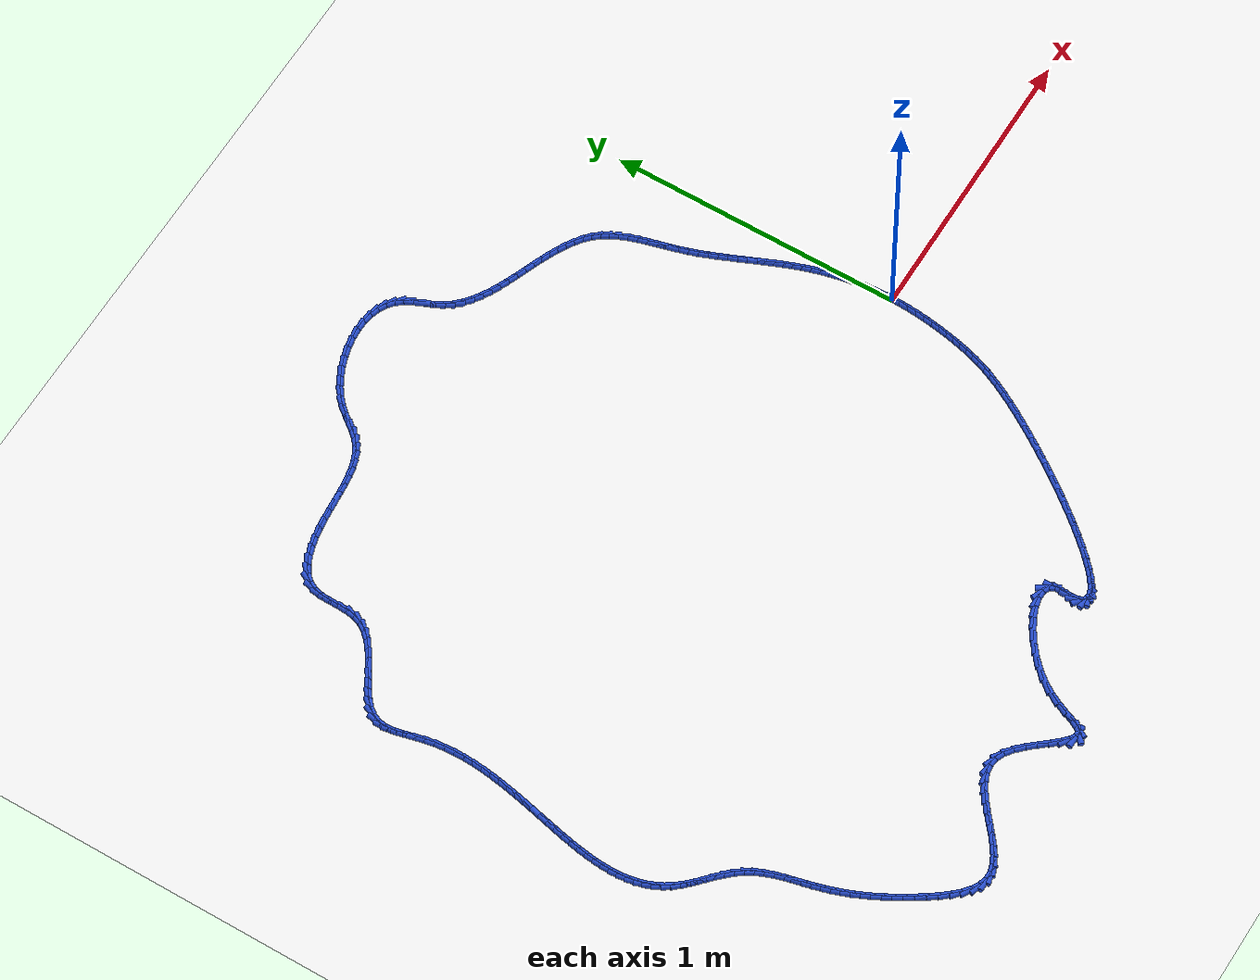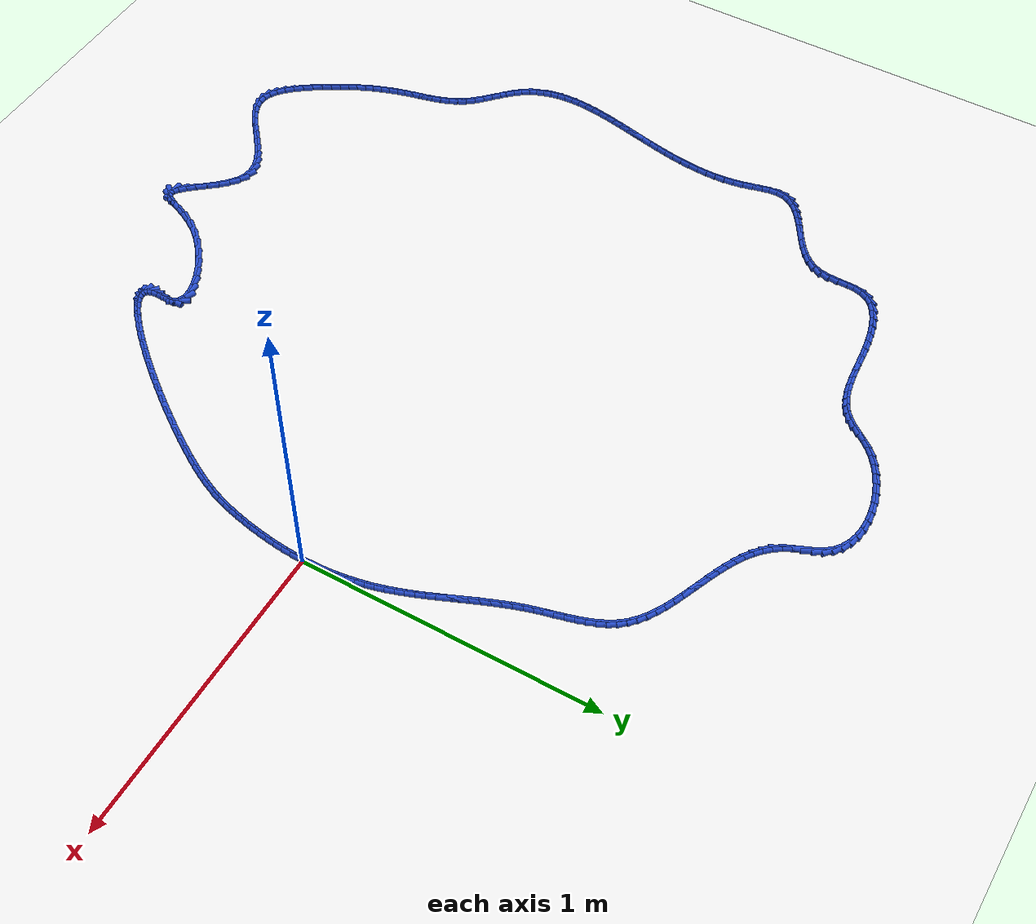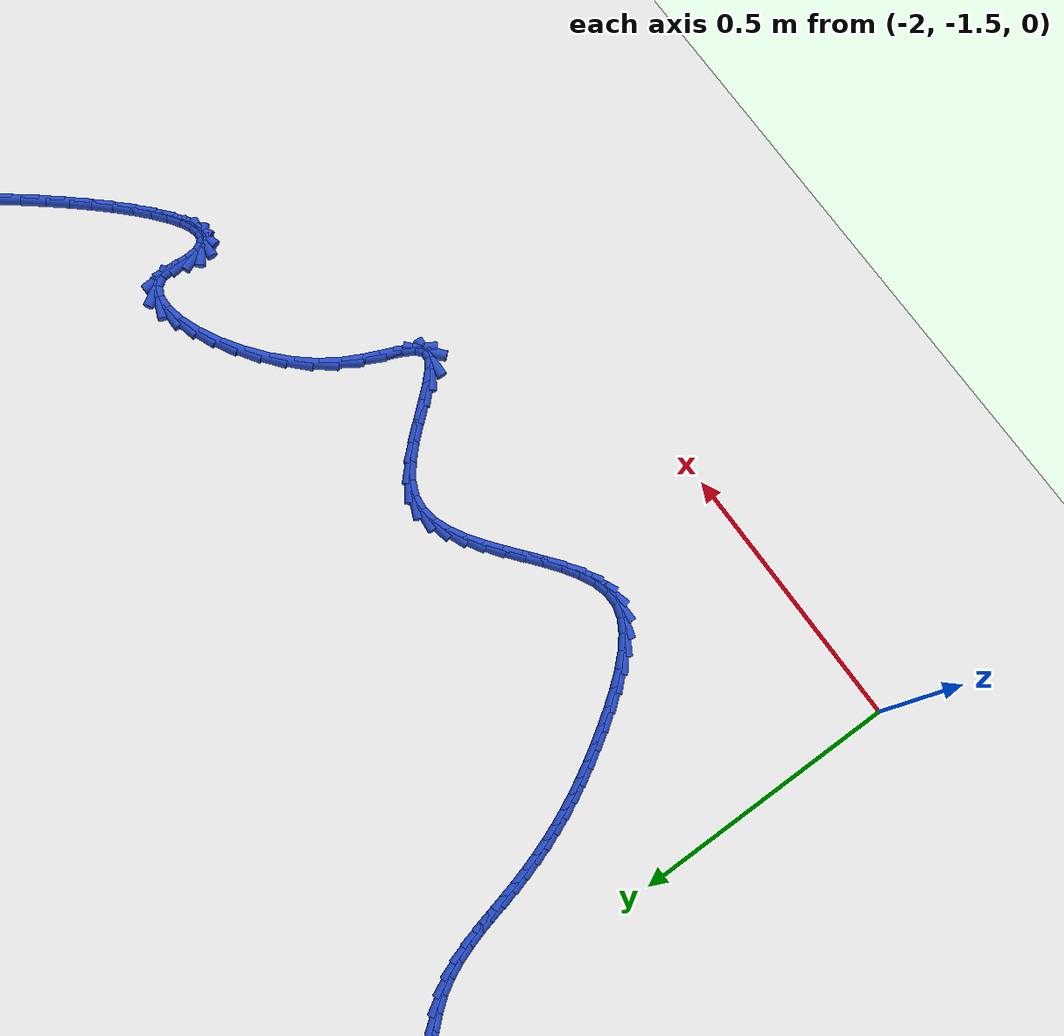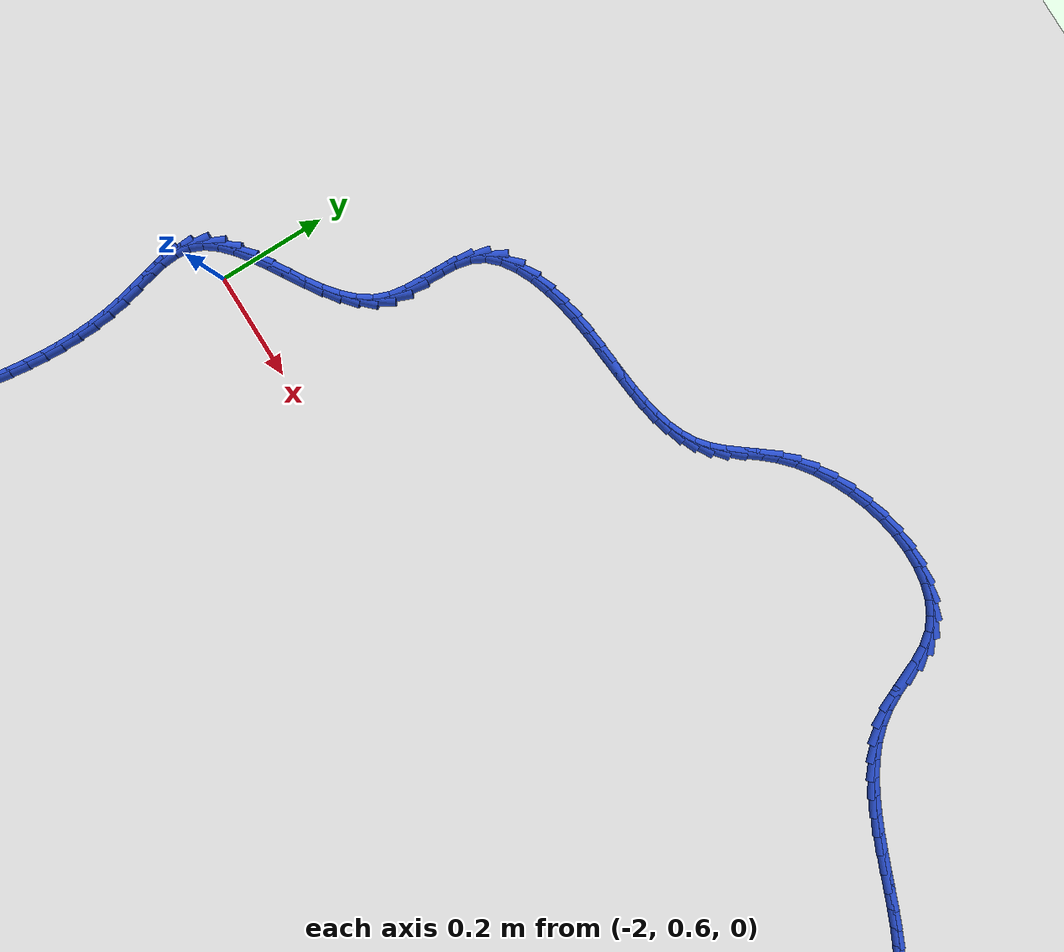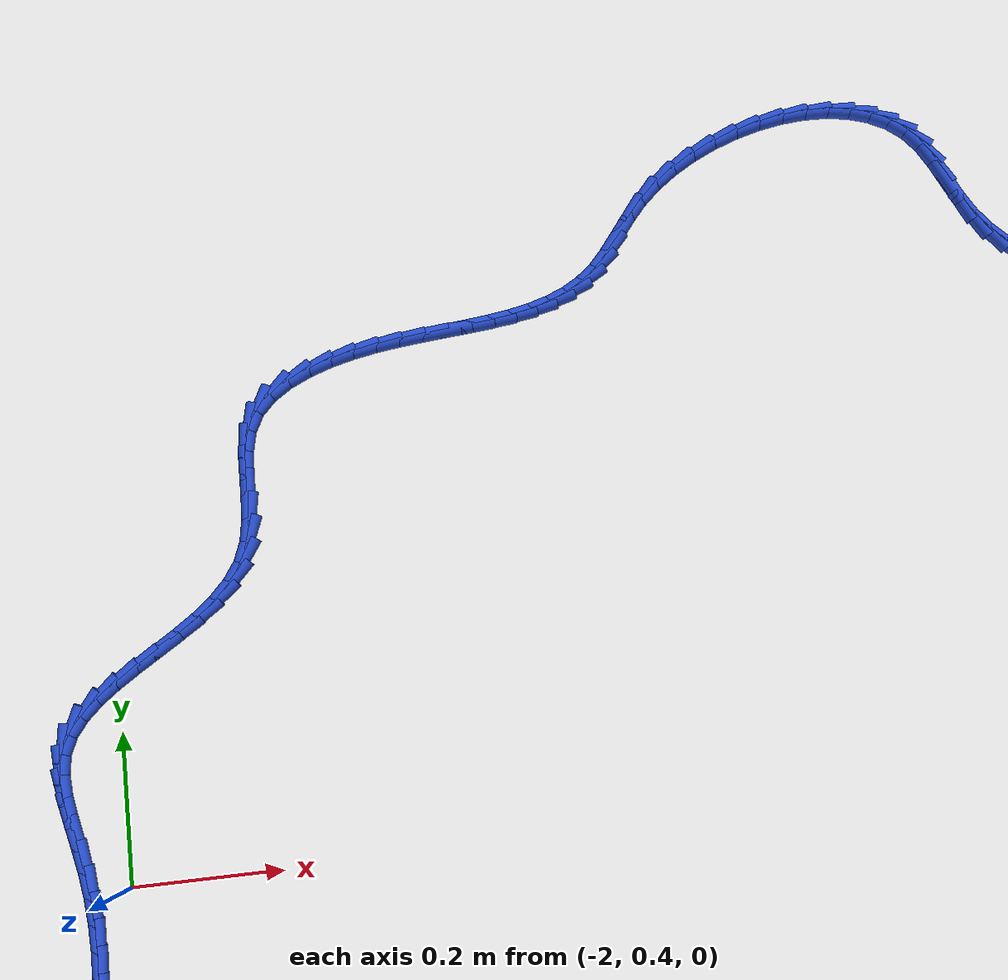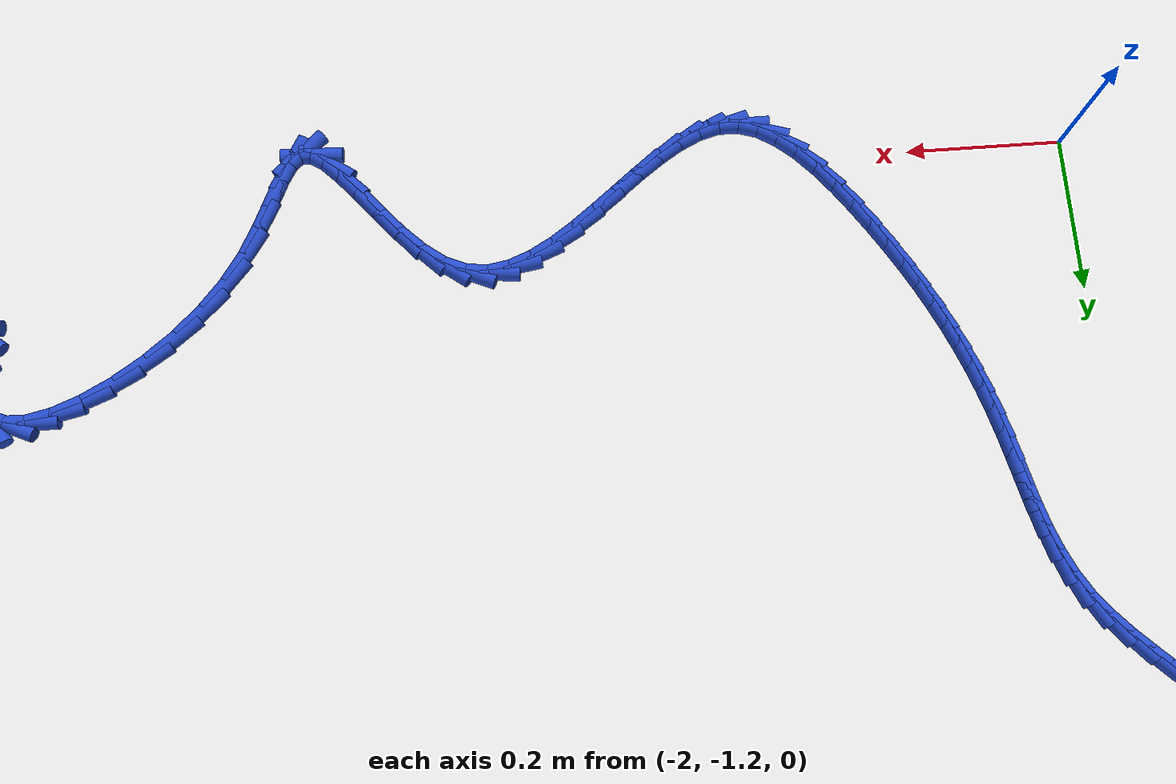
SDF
<sdf version="1.6">
 <world name="default">
  <light name="sun" type="directional">
   <pose>0 0 10 0 -0 0</pose>
   <diffuse>0.8 0.8 0.8 1</diffuse>
   <specular>0.2 0.2 0.2 1</specular>
   <attenuation>
    <range>1000</range>
    <constant>0.9</constant>
    <linear>0.01</linear>
    <quadratic>0.001</quadratic>
   </attenuation>
   <direction>-0.5 0.1 -0.9</direction>
  </light>
  <model name="ground_plane">
   <static>1</static>
   <link name="link">
    <collision name="collision">
     <geometry><plane><normal>0 0 1</normal><size>100 100</size></plane></geometry>
     <surface><friction><ode><mu>100</mu><mu2>50</mu2></ode></friction></surface>
    </collision>
    <visual name="visual">
     <cast_shadows>0</cast_shadows>
     <geometry><plane><normal>0 0 1</normal><size>100 100</size></plane></geometry>
     <material>
      <script><uri>file://media/materials/scripts/gazebo.material</uri><name>Gazebo/WhiteGlow</name></script>
     </material>
    </visual>
   </link>
  </model>
  <gravity>0 0 -9.8</gravity>
  <magnetic_field>6e-06 2.3e-05 -4.2e-05</magnetic_field>
  <atmosphere type="adiabatic"/>
  <physics name="default_physics" default="0" type="ode">
   <max_step_size>0.001</max_step_size>
   <real_time_factor>1</real_time_factor>
   <real_time_update_rate>1000</real_time_update_rate>
  </physics>
  <scene><ambient>0.4 0.4 0.4 1</ambient><background>0.7 0.7 0.7 1</background><shadows>1</shadows></scene>
  <spherical_coordinates>
   <surface_model>EARTH_WGS84</surface_model>
   <latitude_deg>0</latitude_deg>
   <longitude_deg>0</longitude_deg>
   <elevation>0</elevation>
   <heading_deg>0</heading_deg>
  </spherical_coordinates>
  <model name="line">
   <link name="link_0">
    <pose>9.107298248878237e-18 6.938893903907228e-18 0.01 0 1.57 -1.5668264319362275</pose>
    <collision name="collision">
     <geometry><cylinder><radius>0.01</radius><length>0.08</length></cylinder></geometry>
    </collision>
    <visual name="visual">
     <material>
      <script><name>Gazebo/Blue</name><uri>file://media/materials/scripts/gazebo.material</uri></script>
     </material>
     <geometry><cylinder><radius>0.01</radius><length>0.08</length></cylinder></geometry>
    </visual>
   </link>
   <link name="link_1">
    <pose>-0.0001239343897816787 0.03121839321235804 0.01 0 1.57 -1.5336156372987675</pose>
    <collision name="collision">
     <geometry><cylinder><radius>0.01</radius><length>0.08</length></cylinder></geometry>
    </collision>
    <visual name="visual">
     <material>
      <script><name>Gazebo/Blue</name><uri>file://media/materials/scripts/gazebo.material</uri></script>
     </material>
     <geometry><cylinder><radius>0.01</radius><length>0.08</length></cylinder></geometry>
    </visual>
   </link>
   <link name="link_2">
    <pose>-0.0012786598578444545 0.06226120967839678 0.01 0 1.57 -1.5000217866941261</pose>
    <collision name="collision">
     <geometry><cylinder><radius>0.01</radius><length>0.08</length></cylinder></geometry>
    </collision>
    <visual name="visual">
     <material>
      <script><name>Gazebo/Blue</name><uri>file://media/materials/scripts/gazebo.material</uri></script>
     </material>
     <geometry><cylinder><radius>0.01</radius><length>0.08</length></cylinder></geometry>
    </visual>
   </link>
   <link name="link_3">
    <pose>-0.0034647279923184075 0.09309739569848534 0.01 0 1.57 -1.466014178215032</pose>
    <collision name="collision">
     <geometry><cylinder><radius>0.01</radius><length>0.08</length></cylinder></geometry>
    </collision>
    <visual name="visual">
     <material>
      <script><name>Gazebo/Blue</name><uri>file://media/materials/scripts/gazebo.material</uri></script>
     </material>
     <geometry><cylinder><radius>0.01</radius><length>0.08</length></cylinder></geometry>
    </visual>
   </link>
   <link name="link_4">
    <pose>-0.00668269038133363 0.12369589757299287 0.01 0 1.57 -1.431563237630267</pose>
    <collision name="collision">
     <geometry><cylinder><radius>0.01</radius><length>0.08</length></cylinder></geometry>
    </collision>
    <visual name="visual">
     <material>
      <script><name>Gazebo/Blue</name><uri>file://media/materials/scripts/gazebo.material</uri></script>
     </material>
     <geometry><cylinder><radius>0.01</radius><length>0.08</length></cylinder></geometry>
    </visual>
   </link>
   <link name="link_5">
    <pose>-0.010933098613020211 0.15402566160228848 0.01 0 1.57 -1.3966409248389513</pose>
    <collision name="collision">
     <geometry><cylinder><radius>0.01</radius><length>0.08</length></cylinder></geometry>
    </collision>
    <visual name="visual">
     <material>
      <script><name>Gazebo/Blue</name><uri>file://media/materials/scripts/gazebo.material</uri></script>
     </material>
     <geometry><cylinder><radius>0.01</radius><length>0.08</length></cylinder></geometry>
    </visual>
   </link>
   <link name="link_6">
    <pose>-0.016216504275508237 0.1840556340867413 0.01 0 1.57 -1.361221183132592</pose>
    <collision name="collision">
     <geometry><cylinder><radius>0.01</radius><length>0.08</length></cylinder></geometry>
    </collision>
    <visual name="visual">
     <material>
      <script><name>Gazebo/Blue</name><uri>file://media/materials/scripts/gazebo.material</uri></script>
     </material>
     <geometry><cylinder><radius>0.01</radius><length>0.08</length></cylinder></geometry>
    </visual>
   </link>
   <link name="link_7">
    <pose>-0.022533458956927797 0.2137547613267204 0.01 0 1.57 -1.3252804313621547</pose>
    <collision name="collision">
     <geometry><cylinder><radius>0.01</radius><length>0.08</length></cylinder></geometry>
    </collision>
    <visual name="visual">
     <material>
      <script><name>Gazebo/Blue</name><uri>file://media/materials/scripts/gazebo.material</uri></script>
     </material>
     <geometry><cylinder><radius>0.01</radius><length>0.08</length></cylinder></geometry>
    </visual>
   </link>
   <link name="link_8">
    <pose>-0.029884514245408993 0.24309198962259496 0.01 0 1.57 -1.2892531438019739</pose>
    <collision name="collision">
     <geometry><cylinder><radius>0.01</radius><length>0.08</length></cylinder></geometry>
    </collision>
    <visual name="visual">
     <material>
      <script><name>Gazebo/Blue</name><uri>file://media/materials/scripts/gazebo.material</uri></script>
     </material>
     <geometry><cylinder><radius>0.01</radius><length>0.08</length></cylinder></geometry>
    </visual>
   </link>
   <link name="link_9">
    <pose>-0.038258478292713394 0.2720450169516937 0.01 0 1.57 -1.2564737234000498</pose>
    <collision name="collision">
     <geometry><cylinder><radius>0.01</radius><length>0.08</length></cylinder></geometry>
    </collision>
    <visual name="visual">
     <material>
      <script><name>Gazebo/Blue</name><uri>file://media/materials/scripts/gazebo.material</uri></script>
     </material>
     <geometry><cylinder><radius>0.01</radius><length>0.08</length></cylinder></geometry>
    </visual>
   </link>
   <link name="link_10">
    <pose>-0.04755947796184524 0.3006546491637325 0.01 0 1.57 -1.2285402740778695</pose>
    <collision name="collision">
     <geometry><cylinder><radius>0.01</radius><length>0.08</length></cylinder></geometry>
    </collision>
    <visual name="visual">
     <material>
      <script><name>Gazebo/Blue</name><uri>file://media/materials/scripts/gazebo.material</uri></script>
     </material>
     <geometry><cylinder><radius>0.01</radius><length>0.08</length></cylinder></geometry>
    </visual>
   </link>
   <link name="link_11">
    <pose>-0.057654495937476395 0.32898937343095475 0.01 0 1.57 -1.205567716084735</pose>
    <collision name="collision">
     <geometry><cylinder><radius>0.01</radius><length>0.08</length></cylinder></geometry>
    </collision>
    <visual name="visual">
     <material>
      <script><name>Gazebo/Blue</name><uri>file://media/materials/scripts/gazebo.material</uri></script>
     </material>
     <geometry><cylinder><radius>0.01</radius><length>0.08</length></cylinder></geometry>
    </visual>
   </link>
   <link name="link_12">
    <pose>-0.06841035637510524 0.35711779506786373 0.01 0 1.57 -1.1876060721746942</pose>
    <collision name="collision">
     <geometry><cylinder><radius>0.01</radius><length>0.08</length></cylinder></geometry>
    </collision>
    <visual name="visual">
     <material>
      <script><name>Gazebo/Blue</name><uri>file://media/materials/scripts/gazebo.material</uri></script>
     </material>
     <geometry><cylinder><radius>0.01</radius><length>0.08</length></cylinder></geometry>
    </visual>
   </link>
   <link name="link_13">
    <pose>-0.07969388343023011 0.3851085193889631 0.01 0 1.57 -1.1746630989366824</pose>
    <collision name="collision">
     <geometry><cylinder><radius>0.01</radius><length>0.08</length></cylinder></geometry>
    </collision>
    <visual name="visual">
     <material>
      <script><name>Gazebo/Blue</name><uri>file://media/materials/scripts/gazebo.material</uri></script>
     </material>
     <geometry><cylinder><radius>0.01</radius><length>0.08</length></cylinder></geometry>
    </visual>
   </link>
   <link name="link_14">
    <pose>-0.09137190125834933 0.41303015170875623 0.01 0 1.57 -1.1667179222728319</pose>
    <collision name="collision">
     <geometry><cylinder><radius>0.01</radius><length>0.08</length></cylinder></geometry>
    </collision>
    <visual name="visual">
     <material>
      <script><name>Gazebo/Blue</name><uri>file://media/materials/scripts/gazebo.material</uri></script>
     </material>
     <geometry><cylinder><radius>0.01</radius><length>0.08</length></cylinder></geometry>
    </visual>
   </link>
   <link name="link_15">
    <pose>-0.10331123401496135 0.44095129734174665 0.01 0 1.57 -1.1637311236688281</pose>
    <collision name="collision">
     <geometry><cylinder><radius>0.01</radius><length>0.08</length></cylinder></geometry>
    </collision>
    <visual name="visual">
     <material>
      <script><name>Gazebo/Blue</name><uri>file://media/materials/scripts/gazebo.material</uri></script>
     </material>
     <geometry><cylinder><radius>0.01</radius><length>0.08</length></cylinder></geometry>
    </visual>
   </link>
   <link name="link_16">
    <pose>-0.11537870585556448 0.4689405616024379 0.01 0 1.57 -1.1656510495082053</pose>
    <collision name="collision">
     <geometry><cylinder><radius>0.01</radius><length>0.08</length></cylinder></geometry>
    </collision>
    <visual name="visual">
     <material>
      <script><name>Gazebo/Blue</name><uri>file://media/materials/scripts/gazebo.material</uri></script>
     </material>
     <geometry><cylinder><radius>0.01</radius><length>0.08</length></cylinder></geometry>
    </visual>
   </link>
   <link name="link_17">
    <pose>-0.12744114093565703 0.4970665498053333 0.01 0 1.57 -1.1724164000558142</pose>
    <collision name="collision">
     <geometry><cylinder><radius>0.01</radius><length>0.08</length></cylinder></geometry>
    </collision>
    <visual name="visual">
     <material>
      <script><name>Gazebo/Blue</name><uri>file://media/materials/scripts/gazebo.material</uri></script>
     </material>
     <geometry><cylinder><radius>0.01</radius><length>0.08</length></cylinder></geometry>
    </visual>
   </link>
   <link name="link_18">
    <pose>-0.13936536341073744 0.5253978672649364 0.01 0 1.57 -1.1839553151728444</pose>
    <collision name="collision">
     <geometry><cylinder><radius>0.01</radius><length>0.08</length></cylinder></geometry>
    </collision>
    <visual name="visual">
     <material>
      <script><name>Gazebo/Blue</name><uri>file://media/materials/scripts/gazebo.material</uri></script>
     </material>
     <geometry><cylinder><radius>0.01</radius><length>0.08</length></cylinder></geometry>
    </visual>
   </link>
   <link name="link_19">
    <pose>-0.15101819743630393 0.5540031192957506 0.01 0 1.57 -1.2001812779899876</pose>
    <collision name="collision">
     <geometry><cylinder><radius>0.01</radius><length>0.08</length></cylinder></geometry>
    </collision>
    <visual name="visual">
     <material>
      <script><name>Gazebo/Blue</name><uri>file://media/materials/scripts/gazebo.material</uri></script>
     </material>
     <geometry><cylinder><radius>0.01</radius><length>0.08</length></cylinder></geometry>
    </visual>
   </link>
   <link name="link_20">
    <pose>-0.1622664671678551 0.5829509112122796 0.01 0 1.57 -1.2209862667133176</pose>
    <collision name="collision">
     <geometry><cylinder><radius>0.01</radius><length>0.08</length></cylinder></geometry>
    </collision>
    <visual name="visual">
     <material>
      <script><name>Gazebo/Blue</name><uri>file://media/materials/scripts/gazebo.material</uri></script>
     </material>
     <geometry><cylinder><radius>0.01</radius><length>0.08</length></cylinder></geometry>
    </visual>
   </link>
   <link name="link_21">
    <pose>-0.17297699676088907 0.6123098483290267 0.01 0 1.57 -1.2462317444198887</pose>
    <collision name="collision">
     <geometry><cylinder><radius>0.01</radius><length>0.08</length></cylinder></geometry>
    </collision>
    <visual name="visual">
     <material>
      <script><name>Gazebo/Blue</name><uri>file://media/materials/scripts/gazebo.material</uri></script>
     </material>
     <geometry><cylinder><radius>0.01</radius><length>0.08</length></cylinder></geometry>
    </visual>
   </link>
   <link name="link_22">
    <pose>-0.18301661037090433 0.6421485359604955 0.01 0 1.57 -1.2757020626371696</pose>
    <collision name="collision">
     <geometry><cylinder><radius>0.01</radius><length>0.08</length></cylinder></geometry>
    </collision>
    <visual name="visual">
     <material>
      <script><name>Gazebo/Blue</name><uri>file://media/materials/scripts/gazebo.material</uri></script>
     </material>
     <geometry><cylinder><radius>0.01</radius><length>0.08</length></cylinder></geometry>
    </visual>
   </link>
   <link name="link_23">
    <pose>-0.19225311509002324 0.6725348547015699 0.01 0 1.57 -1.3028874422926053</pose>
    <collision name="collision">
     <geometry><cylinder><radius>0.01</radius><length>0.08</length></cylinder></geometry>
    </collision>
    <visual name="visual">
     <material>
      <script><name>Gazebo/Blue</name><uri>file://media/materials/scripts/gazebo.material</uri></script>
     </material>
     <geometry><cylinder><radius>0.01</radius><length>0.08</length></cylinder></geometry>
    </visual>
   </link>
   <link name="link_24">
    <pose>-0.20072818118188515 0.7034084957517882 0.01 0 1.57 -1.3145975768397777</pose>
    <collision name="collision">
     <geometry><cylinder><radius>0.01</radius><length>0.08</length></cylinder></geometry>
    </collision>
    <visual name="visual">
     <material>
      <script><name>Gazebo/Blue</name><uri>file://media/materials/scripts/gazebo.material</uri></script>
     </material>
     <geometry><cylinder><radius>0.01</radius><length>0.08</length></cylinder></geometry>
    </visual>
   </link>
   <link name="link_25">
    <pose>-0.20885567091452198 0.7344347329767632 0.01 0 1.57 -1.3094022620440617</pose>
    <collision name="collision">
     <geometry><cylinder><radius>0.01</radius><length>0.08</length></cylinder></geometry>
    </collision>
    <visual name="visual">
     <material>
      <script><name>Gazebo/Blue</name><uri>file://media/materials/scripts/gazebo.material</uri></script>
     </material>
     <geometry><cylinder><radius>0.01</radius><length>0.08</length></cylinder></geometry>
    </visual>
   </link>
   <link name="link_26">
    <pose>-0.21709745705123953 0.7652434420821306 0.01 0 1.57 -1.286896083961144</pose>
    <collision name="collision">
     <geometry><cylinder><radius>0.01</radius><length>0.08</length></cylinder></geometry>
    </collision>
    <visual name="visual">
     <material>
      <script><name>Gazebo/Blue</name><uri>file://media/materials/scripts/gazebo.material</uri></script>
     </material>
     <geometry><cylinder><radius>0.01</radius><length>0.08</length></cylinder></geometry>
    </visual>
   </link>
   <link name="link_27">
    <pose>-0.22591541235534365 0.7954644987735261 0.01 0 1.57 -1.2459252017623088</pose>
    <collision name="collision">
     <geometry><cylinder><radius>0.01</radius><length>0.08</length></cylinder></geometry>
    </collision>
    <visual name="visual">
     <material>
      <script><name>Gazebo/Blue</name><uri>file://media/materials/scripts/gazebo.material</uri></script>
     </material>
     <geometry><cylinder><radius>0.01</radius><length>0.08</length></cylinder></geometry>
    </visual>
   </link>
   <link name="link_28">
    <pose>-0.23577140959014015 0.824727778756586 0.01 0 1.57 -1.1846935498686706</pose>
    <collision name="collision">
     <geometry><cylinder><radius>0.01</radius><length>0.08</length></cylinder></geometry>
    </collision>
    <visual name="visual">
     <material>
      <script><name>Gazebo/Blue</name><uri>file://media/materials/scripts/gazebo.material</uri></script>
     </material>
     <geometry><cylinder><radius>0.01</radius><length>0.08</length></cylinder></geometry>
    </visual>
   </link>
   <link name="link_29">
    <pose>-0.247127321518935 0.8526631577369461 0.01 0 1.57 -1.1010987759824464</pose>
    <collision name="collision">
     <geometry><cylinder><radius>0.01</radius><length>0.08</length></cylinder></geometry>
    </collision>
    <visual name="visual">
     <material>
      <script><name>Gazebo/Blue</name><uri>file://media/materials/scripts/gazebo.material</uri></script>
     </material>
     <geometry><cylinder><radius>0.01</radius><length>0.08</length></cylinder></geometry>
    </visual>
   </link>
   <link name="link_30">
    <pose>-0.2604450209050338 0.8789005114202417 0.01 0 1.57 -0.993509014747664</pose>
    <collision name="collision">
     <geometry><cylinder><radius>0.01</radius><length>0.08</length></cylinder></geometry>
    </collision>
    <visual name="visual">
     <material>
      <script><name>Gazebo/Blue</name><uri>file://media/materials/scripts/gazebo.material</uri></script>
     </material>
     <geometry><cylinder><radius>0.01</radius><length>0.08</length></cylinder></geometry>
    </visual>
   </link>
   <link name="link_31">
    <pose>-0.27618638051174255 0.9030697155121088 0.01 0 1.57 -0.8647516929594672</pose>
    <collision name="collision">
     <geometry><cylinder><radius>0.01</radius><length>0.08</length></cylinder></geometry>
    </collision>
    <visual name="visual">
     <material>
      <script><name>Gazebo/Blue</name><uri>file://media/materials/scripts/gazebo.material</uri></script>
     </material>
     <geometry><cylinder><radius>0.01</radius><length>0.08</length></cylinder></geometry>
    </visual>
   </link>
   <link name="link_32">
    <pose>-0.2947563008786647 0.9248481584157575 0.01 0 1.57 -0.7406093928511145</pose>
    <collision name="collision">
     <geometry><cylinder><radius>0.01</radius><length>0.08</length></cylinder></geometry>
    </collision>
    <visual name="visual">
     <material>
      <script><name>Gazebo/Blue</name><uri>file://media/materials/scripts/gazebo.material</uri></script>
     </material>
     <geometry><cylinder><radius>0.01</radius><length>0.08</length></cylinder></geometry>
    </visual>
   </link>
   <link name="link_33">
    <pose>-0.3160633077837087 0.9443271864669287 0.01 0 1.57 -0.6356681920507704</pose>
    <collision name="collision">
     <geometry><cylinder><radius>0.01</radius><length>0.08</length></cylinder></geometry>
    </collision>
    <visual name="visual">
     <material>
      <script><name>Gazebo/Blue</name><uri>file://media/materials/scripts/gazebo.material</uri></script>
     </material>
     <geometry><cylinder><radius>0.01</radius><length>0.08</length></cylinder></geometry>
    </visual>
   </link>
   <link name="link_34">
    <pose>-0.3397601324169409 0.9618114690929219 0.01 0 1.57 -0.5504610401595924</pose>
    <collision name="collision">
     <geometry><cylinder><radius>0.01</radius><length>0.08</length></cylinder></geometry>
    </collision>
    <visual name="visual">
     <material>
      <script><name>Gazebo/Blue</name><uri>file://media/materials/scripts/gazebo.material</uri></script>
     </material>
     <geometry><cylinder><radius>0.01</radius><length>0.08</length></cylinder></geometry>
    </visual>
   </link>
   <link name="link_35">
    <pose>-0.3654973855572271 0.977607444064442 0.01 0 1.57 -0.4838542391473702</pose>
    <collision name="collision">
     <geometry><cylinder><radius>0.01</radius><length>0.08</length></cylinder></geometry>
    </collision>
    <visual name="visual">
     <material>
      <script><name>Gazebo/Blue</name><uri>file://media/materials/scripts/gazebo.material</uri></script>
     </material>
     <geometry><cylinder><radius>0.01</radius><length>0.08</length></cylinder></geometry>
    </visual>
   </link>
   <link name="link_36">
    <pose>-0.39292567798343325 0.992021549152194 0.01 0 1.57 -0.4341324930475054</pose>
    <collision name="collision">
     <geometry><cylinder><radius>0.01</radius><length>0.08</length></cylinder></geometry>
    </collision>
    <visual name="visual">
     <material>
      <script><name>Gazebo/Blue</name><uri>file://media/materials/scripts/gazebo.material</uri></script>
     </material>
     <geometry><cylinder><radius>0.01</radius><length>0.08</length></cylinder></geometry>
    </visual>
   </link>
   <link name="link_37">
    <pose>-0.42169562047442494 1.0053602221268827 0.01 0 1.57 -0.3996128723988343</pose>
    <collision name="collision">
     <geometry><cylinder><radius>0.01</radius><length>0.08</length></cylinder></geometry>
    </collision>
    <visual name="visual">
     <material>
      <script><name>Gazebo/Blue</name><uri>file://media/materials/scripts/gazebo.material</uri></script>
     </material>
     <geometry><cylinder><radius>0.01</radius><length>0.08</length></cylinder></geometry>
    </visual>
   </link>
   <link name="link_38">
    <pose>-0.45145782380906857 1.0179299007592137 0.01 0 1.57 -0.37894861506903343</pose>
    <collision name="collision">
     <geometry><cylinder><radius>0.01</radius><length>0.08</length></cylinder></geometry>
    </collision>
    <visual name="visual">
     <material>
      <script><name>Gazebo/Blue</name><uri>file://media/materials/scripts/gazebo.material</uri></script>
     </material>
     <geometry><cylinder><radius>0.01</radius><length>0.08</length></cylinder></geometry>
    </visual>
   </link>
   <link name="link_39">
    <pose>-0.4818628987662297 1.0300370228198916 0.01 0 1.57 -0.37124989619854165</pose>
    <collision name="collision">
     <geometry><cylinder><radius>0.01</radius><length>0.08</length></cylinder></geometry>
    </collision>
    <visual name="visual">
     <material>
      <script><name>Gazebo/Blue</name><uri>file://media/materials/scripts/gazebo.material</uri></script>
     </material>
     <geometry><cylinder><radius>0.01</radius><length>0.08</length></cylinder></geometry>
    </visual>
   </link>
   <link name="link_40">
    <pose>-0.5125614561247741 1.0419880260796215 0.01 0 1.57 -0.37611734015171594</pose>
    <collision name="collision">
     <geometry><cylinder><radius>0.01</radius><length>0.08</length></cylinder></geometry>
    </collision>
    <visual name="visual">
     <material>
      <script><name>Gazebo/Blue</name><uri>file://media/materials/scripts/gazebo.material</uri></script>
     </material>
     <geometry><cylinder><radius>0.01</radius><length>0.08</length></cylinder></geometry>
    </visual>
   </link>
   <link name="link_41">
    <pose>-0.5432041066635681 1.0540893483091085 0.01 0 1.57 -0.3936403204589608</pose>
    <collision name="collision">
     <geometry><cylinder><radius>0.01</radius><length>0.08</length></cylinder></geometry>
    </collision>
    <visual name="visual">
     <material>
      <script><name>Gazebo/Blue</name><uri>file://media/materials/scripts/gazebo.material</uri></script>
     </material>
     <geometry><cylinder><radius>0.01</radius><length>0.08</length></cylinder></geometry>
    </visual>
   </link>
   <link name="link_42">
    <pose>-0.5734414611614773 1.0666474272790578 0.01 0 1.57 -0.4243780661051072</pose>
    <collision name="collision">
     <geometry><cylinder><radius>0.01</radius><length>0.08</length></cylinder></geometry>
    </collision>
    <visual name="visual">
     <material>
      <script><name>Gazebo/Blue</name><uri>file://media/materials/scripts/gazebo.material</uri></script>
     </material>
     <geometry><cylinder><radius>0.01</radius><length>0.08</length></cylinder></geometry>
    </visual>
   </link>
   <link name="link_43">
    <pose>-0.6029241303973674 1.0799687007601737 0.01 0 1.57 -0.46931483670298435</pose>
    <collision name="collision">
     <geometry><cylinder><radius>0.01</radius><length>0.08</length></cylinder></geometry>
    </collision>
    <visual name="visual">
     <material>
      <script><name>Gazebo/Blue</name><uri>file://media/materials/scripts/gazebo.material</uri></script>
     </material>
     <geometry><cylinder><radius>0.01</radius><length>0.08</length></cylinder></geometry>
    </visual>
   </link>
   <link name="link_44">
    <pose>-0.6313027251501041 1.0943596065231618 0.01 0 1.57 -0.5297534367914862</pose>
    <collision name="collision">
     <geometry><cylinder><radius>0.01</radius><length>0.08</length></cylinder></geometry>
    </collision>
    <visual name="visual">
     <material>
      <script><name>Gazebo/Blue</name><uri>file://media/materials/scripts/gazebo.material</uri></script>
     </material>
     <geometry><cylinder><radius>0.01</radius><length>0.08</length></cylinder></geometry>
    </visual>
   </link>
   <link name="link_45">
    <pose>-0.6582278561985538 1.110126582338727 0.01 0 1.57 -0.6070804988161297</pose>
    <collision name="collision">
     <geometry><cylinder><radius>0.01</radius><length>0.08</length></cylinder></geometry>
    </collision>
    <visual name="visual">
     <material>
      <script><name>Gazebo/Blue</name><uri>file://media/materials/scripts/gazebo.material</uri></script>
     </material>
     <geometry><cylinder><radius>0.01</radius><length>0.08</length></cylinder></geometry>
    </visual>
   </link>
   <link name="link_46">
    <pose>-0.6833501343215828 1.1275760659775749 0.01 0 1.57 -0.7023138838810022</pose>
    <collision name="collision">
     <geometry><cylinder><radius>0.01</radius><length>0.08</length></cylinder></geometry>
    </collision>
    <visual name="visual">
     <material>
      <script><name>Gazebo/Blue</name><uri>file://media/materials/scripts/gazebo.material</uri></script>
     </material>
     <geometry><cylinder><radius>0.01</radius><length>0.08</length></cylinder></geometry>
    </visual>
   </link>
   <link name="link_47">
    <pose>-0.7063201702980559 1.1470144952104098 0.01 0 1.57 -0.8153735781821636</pose>
    <collision name="collision">
     <geometry><cylinder><radius>0.01</radius><length>0.08</length></cylinder></geometry>
    </collision>
    <visual name="visual">
     <material>
      <script><name>Gazebo/Blue</name><uri>file://media/materials/scripts/gazebo.material</uri></script>
     </material>
     <geometry><cylinder><radius>0.01</radius><length>0.08</length></cylinder></geometry>
    </visual>
   </link>
   <link name="link_48">
    <pose>-0.7267885749068392 1.1687483078079366 0.01 0 1.57 -0.944187451818332</pose>
    <collision name="collision">
     <geometry><cylinder><radius>0.01</radius><length>0.08</length></cylinder></geometry>
    </collision>
    <visual name="visual">
     <material>
      <script><name>Gazebo/Blue</name><uri>file://media/materials/scripts/gazebo.material</uri></script>
     </material>
     <geometry><cylinder><radius>0.01</radius><length>0.08</length></cylinder></geometry>
    </visual>
   </link>
   <link name="link_49">
    <pose>-0.7444059589267992 1.193083941540861 0.01 0 1.57 -1.0778306875273709</pose>
    <collision name="collision">
     <geometry><cylinder><radius>0.01</radius><length>0.08</length></cylinder></geometry>
    </collision>
    <visual name="visual">
     <material>
      <script><name>Gazebo/Blue</name><uri>file://media/materials/scripts/gazebo.material</uri></script>
     </material>
     <geometry><cylinder><radius>0.01</radius><length>0.08</length></cylinder></geometry>
    </visual>
   </link>
   <link name="link_50">
    <pose>-0.7589664634326562 1.2201882004132607 0.01 0 1.57 -1.1568648756387585</pose>
    <collision name="collision">
     <geometry><cylinder><radius>0.01</radius><length>0.08</length></cylinder></geometry>
    </collision>
    <visual name="visual">
     <material>
      <script><name>Gazebo/Blue</name><uri>file://media/materials/scripts/gazebo.material</uri></script>
     </material>
     <geometry><cylinder><radius>0.01</radius><length>0.08</length></cylinder></geometry>
    </visual>
   </link>
   <link name="link_51">
    <pose>-0.7715946815111623 1.2489335552387961 0.01 0 1.57 -1.1569846791971388</pose>
    <collision name="collision">
     <geometry><cylinder><radius>0.01</radius><length>0.08</length></cylinder></geometry>
    </collision>
    <visual name="visual">
     <material>
      <script><name>Gazebo/Blue</name><uri>file://media/materials/scripts/gazebo.material</uri></script>
     </material>
     <geometry><cylinder><radius>0.01</radius><length>0.08</length></cylinder></geometry>
    </visual>
   </link>
   <link name="link_52">
    <pose>-0.7841362641954972 1.2774909940088681 0.01 0 1.57 -1.076258914075671</pose>
    <collision name="collision">
     <geometry><cylinder><radius>0.01</radius><length>0.08</length></cylinder></geometry>
    </collision>
    <visual name="visual">
     <material>
      <script><name>Gazebo/Blue</name><uri>file://media/materials/scripts/gazebo.material</uri></script>
     </material>
     <geometry><cylinder><radius>0.01</radius><length>0.08</length></cylinder></geometry>
    </visual>
   </link>
   <link name="link_53">
    <pose>-0.7984439847052462 1.3040245758800404 0.01 0 1.57 -0.9031424003588444</pose>
    <collision name="collision">
     <geometry><cylinder><radius>0.01</radius><length>0.08</length></cylinder></geometry>
    </collision>
    <visual name="visual">
     <material>
      <script><name>Gazebo/Blue</name><uri>file://media/materials/scripts/gazebo.material</uri></script>
     </material>
     <geometry><cylinder><radius>0.01</radius><length>0.08</length></cylinder></geometry>
    </visual>
   </link>
   <link name="link_54">
    <pose>-0.8163404963824495 1.3267231351371294 0.01 0 1.57 -0.6783900038247324</pose>
    <collision name="collision">
     <geometry><cylinder><radius>0.01</radius><length>0.08</length></cylinder></geometry>
    </collision>
    <visual name="visual">
     <material>
      <script><name>Gazebo/Blue</name><uri>file://media/materials/scripts/gazebo.material</uri></script>
     </material>
     <geometry><cylinder><radius>0.01</radius><length>0.08</length></cylinder></geometry>
    </visual>
   </link>
   <link name="link_55">
    <pose>-0.8385837719429866 1.344651259926257 0.01 0 1.57 -0.4728296312682994</pose>
    <collision name="collision">
     <geometry><cylinder><radius>0.01</radius><length>0.08</length></cylinder></geometry>
    </collision>
    <visual name="visual">
     <material>
      <script><name>Gazebo/Blue</name><uri>file://media/materials/scripts/gazebo.material</uri></script>
     </material>
     <geometry><cylinder><radius>0.01</radius><length>0.08</length></cylinder></geometry>
    </visual>
   </link>
   <link name="link_56">
    <pose>-0.8646072235535318 1.3579630566838135 0.01 0 1.57 -0.2968446338213762</pose>
    <collision name="collision">
     <geometry><cylinder><radius>0.01</radius><length>0.08</length></cylinder></geometry>
    </collision>
    <visual name="visual">
     <material>
      <script><name>Gazebo/Blue</name><uri>file://media/materials/scripts/gazebo.material</uri></script>
     </material>
     <geometry><cylinder><radius>0.01</radius><length>0.08</length></cylinder></geometry>
    </visual>
   </link>
   <link name="link_57">
    <pose>-0.8937613890742512 1.3668808001702364 0.01 0 1.57 -0.148910115655145</pose>
    <collision name="collision">
     <geometry><cylinder><radius>0.01</radius><length>0.08</length></cylinder></geometry>
    </collision>
    <visual name="visual">
     <material>
      <script><name>Gazebo/Blue</name><uri>file://media/materials/scripts/gazebo.material</uri></script>
     </material>
     <geometry><cylinder><radius>0.01</radius><length>0.08</length></cylinder></geometry>
    </visual>
   </link>
   <link name="link_58">
    <pose>-0.92539680636531 1.371626765145961 0.01 0 1.57 -0.023793766773452747</pose>
    <collision name="collision">
     <geometry><cylinder><radius>0.01</radius><length>0.08</length></cylinder></geometry>
    </collision>
    <visual name="visual">
     <material>
      <script><name>Gazebo/Blue</name><uri>file://media/materials/scripts/gazebo.material</uri></script>
     </material>
     <geometry><cylinder><radius>0.01</radius><length>0.08</length></cylinder></geometry>
    </visual>
   </link>
   <link name="link_59">
    <pose>-0.9588640132868739 1.3724232263714236 0.01 0 1.57 0.08438232871574575</pose>
    <collision name="collision">
     <geometry><cylinder><radius>0.01</radius><length>0.08</length></cylinder></geometry>
    </collision>
    <visual name="visual">
     <material>
      <script><name>Gazebo/Blue</name><uri>file://media/materials/scripts/gazebo.material</uri></script>
     </material>
     <geometry><cylinder><radius>0.01</radius><length>0.08</length></cylinder></geometry>
    </visual>
   </link>
   <link name="link_60">
    <pose>-0.9935135476991082 1.369492458607061 0.01 0 1.57 0.18092418237907804</pose>
    <collision name="collision">
     <geometry><cylinder><radius>0.01</radius><length>0.08</length></cylinder></geometry>
    </collision>
    <visual name="visual">
     <material>
      <script><name>Gazebo/Blue</name><uri>file://media/materials/scripts/gazebo.material</uri></script>
     </material>
     <geometry><cylinder><radius>0.01</radius><length>0.08</length></cylinder></geometry>
    </visual>
   </link>
   <link name="link_61">
    <pose>-1.028695947462179 1.3630567366133084 0.01 0 1.57 0.27036167488859647</pose>
    <collision name="collision">
     <geometry><cylinder><radius>0.01</radius><length>0.08</length></cylinder></geometry>
    </collision>
    <visual name="visual">
     <material>
      <script><name>Gazebo/Blue</name><uri>file://media/materials/scripts/gazebo.material</uri></script>
     </material>
     <geometry><cylinder><radius>0.01</radius><length>0.08</length></cylinder></geometry>
    </visual>
   </link>
   <link name="link_62">
    <pose>-1.0637617504362515 1.3533383351506028 0.01 0 1.57 0.3566321725270101</pose>
    <collision name="collision">
     <geometry><cylinder><radius>0.01</radius><length>0.08</length></cylinder></geometry>
    </collision>
    <visual name="visual">
     <material>
      <script><name>Gazebo/Blue</name><uri>file://media/materials/scripts/gazebo.material</uri></script>
     </material>
     <geometry><cylinder><radius>0.01</radius><length>0.08</length></cylinder></geometry>
    </visual>
   </link>
   <link name="link_63">
    <pose>-1.098061494481492 1.34055952897938 0.01 0 1.57 0.44337216714333494</pose>
    <collision name="collision">
     <geometry><cylinder><radius>0.01</radius><length>0.08</length></cylinder></geometry>
    </collision>
    <visual name="visual">
     <material>
      <script><name>Gazebo/Blue</name><uri>file://media/materials/scripts/gazebo.material</uri></script>
     </material>
     <geometry><cylinder><radius>0.01</radius><length>0.08</length></cylinder></geometry>
    </visual>
   </link>
   <link name="link_64">
    <pose>-1.130945717458065 1.3249425928600767 0.01 0 1.57 0.5342232366662157</pose>
    <collision name="collision">
     <geometry><cylinder><radius>0.01</radius><length>0.08</length></cylinder></geometry>
    </collision>
    <visual name="visual">
     <material>
      <script><name>Gazebo/Blue</name><uri>file://media/materials/scripts/gazebo.material</uri></script>
     </material>
     <geometry><cylinder><radius>0.01</radius><length>0.08</length></cylinder></geometry>
    </visual>
   </link>
   <link name="link_65">
    <pose>-1.1617649572261366 1.306709801553128 0.01 0 1.57 0.6331233170564774</pose>
    <collision name="collision">
     <geometry><cylinder><radius>0.01</radius><length>0.08</length></cylinder></geometry>
    </collision>
    <visual name="visual">
     <material>
      <script><name>Gazebo/Blue</name><uri>file://media/materials/scripts/gazebo.material</uri></script>
     </material>
     <geometry><cylinder><radius>0.01</radius><length>0.08</length></cylinder></geometry>
    </visual>
   </link>
   <link name="link_66">
    <pose>-1.1898697516458727 1.2860834298189712 0.01 0 1.57 0.7445180227827529</pose>
    <collision name="collision">
     <geometry><cylinder><radius>0.01</radius><length>0.08</length></cylinder></geometry>
    </collision>
    <visual name="visual">
     <material>
      <script><name>Gazebo/Blue</name><uri>file://media/materials/scripts/gazebo.material</uri></script>
     </material>
     <geometry><cylinder><radius>0.01</radius><length>0.08</length></cylinder></geometry>
    </visual>
   </link>
   <link name="link_67">
    <pose>-1.2146114518813442 1.263286210612098 0.01 0 1.57 0.8551568165661251</pose>
    <collision name="collision">
     <geometry><cylinder><radius>0.01</radius><length>0.08</length></cylinder></geometry>
    </collision>
    <visual name="visual">
     <material>
      <script><name>Gazebo/Blue</name><uri>file://media/materials/scripts/gazebo.material</uri></script>
     </material>
     <geometry><cylinder><radius>0.01</radius><length>0.08</length></cylinder></geometry>
    </visual>
   </link>
   <link name="link_68">
    <pose>-1.235867122943851 1.2388370502586945 0.01 0 1.57 0.9146644474738805</pose>
    <collision name="collision">
     <geometry><cylinder><radius>0.01</radius><length>0.08</length></cylinder></geometry>
    </collision>
    <visual name="visual">
     <material>
      <script><name>Gazebo/Blue</name><uri>file://media/materials/scripts/gazebo.material</uri></script>
     </material>
     <geometry><cylinder><radius>0.01</radius><length>0.08</length></cylinder></geometry>
    </visual>
   </link>
   <link name="link_69">
    <pose>-1.2549434142028086 1.214060245358944 0.01 0 1.57 0.9083300814473821</pose>
    <collision name="collision">
     <geometry><cylinder><radius>0.01</radius><length>0.08</length></cylinder></geometry>
    </collision>
    <visual name="visual">
     <material>
      <script><name>Gazebo/Blue</name><uri>file://media/materials/scripts/gazebo.material</uri></script>
     </material>
     <geometry><cylinder><radius>0.01</radius><length>0.08</length></cylinder></geometry>
    </visual>
   </link>
   <link name="link_70">
    <pose>-1.2733876796332058 1.1904156991648056 0.01 0 1.57 0.8272620294305417</pose>
    <collision name="collision">
     <geometry><cylinder><radius>0.01</radius><length>0.08</length></cylinder></geometry>
    </collision>
    <visual name="visual">
     <material>
      <script><name>Gazebo/Blue</name><uri>file://media/materials/scripts/gazebo.material</uri></script>
     </material>
     <geometry><cylinder><radius>0.01</radius><length>0.08</length></cylinder></geometry>
    </visual>
   </link>
   <link name="link_71">
    <pose>-1.2927472732100296 1.1693633149282376 0.01 0 1.57 0.6763125241229873</pose>
    <collision name="collision">
     <geometry><cylinder><radius>0.01</radius><length>0.08</length></cylinder></geometry>
    </collision>
    <visual name="visual">
     <material>
      <script><name>Gazebo/Blue</name><uri>file://media/materials/scripts/gazebo.material</uri></script>
     </material>
     <geometry><cylinder><radius>0.01</radius><length>0.08</length></cylinder></geometry>
    </visual>
   </link>
   <link name="link_72">
    <pose>-1.3142991769995678 1.1520661741702618 0.01 0 1.57 0.521705374915482</pose>
    <collision name="collision">
     <geometry><cylinder><radius>0.01</radius><length>0.08</length></cylinder></geometry>
    </collision>
    <visual name="visual">
     <material>
      <script><name>Gazebo/Blue</name><uri>file://media/materials/scripts/gazebo.material</uri></script>
     </material>
     <geometry><cylinder><radius>0.01</radius><length>0.08</length></cylinder></geometry>
    </visual>
   </link>
   <link name="link_73">
    <pose>-1.3381222304066607 1.1383720043857015 0.01 0 1.57 0.38952080807354994</pose>
    <collision name="collision">
     <geometry><cylinder><radius>0.01</radius><length>0.08</length></cylinder></geometry>
    </collision>
    <visual name="visual">
     <material>
      <script><name>Gazebo/Blue</name><uri>file://media/materials/scripts/gazebo.material</uri></script>
     </material>
     <geometry><cylinder><radius>0.01</radius><length>0.08</length></cylinder></geometry>
    </visual>
   </link>
   <link name="link_74">
    <pose>-1.3639634948093373 1.127764298010054 0.01 0 1.57 0.2833220206624581</pose>
    <collision name="collision">
     <geometry><cylinder><radius>0.01</radius><length>0.08</length></cylinder></geometry>
    </collision>
    <visual name="visual">
     <material>
      <script><name>Gazebo/Blue</name><uri>file://media/materials/scripts/gazebo.material</uri></script>
     </material>
     <geometry><cylinder><radius>0.01</radius><length>0.08</length></cylinder></geometry>
    </visual>
   </link>
   <link name="link_75">
    <pose>-1.3915700196650418 1.1197265343920733 0.01 0 1.57 0.20269225563554946</pose>
    <collision name="collision">
     <geometry><cylinder><radius>0.01</radius><length>0.08</length></cylinder></geometry>
    </collision>
    <visual name="visual">
     <material>
      <script><name>Gazebo/Blue</name><uri>file://media/materials/scripts/gazebo.material</uri></script>
     </material>
     <geometry><cylinder><radius>0.01</radius><length>0.08</length></cylinder></geometry>
    </visual>
   </link>
   <link name="link_76">
    <pose>-1.420688854431221 1.1137421928805131 0.01 0 1.57 0.14536965382685466</pose>
    <collision name="collision">
     <geometry><cylinder><radius>0.01</radius><length>0.08</length></cylinder></geometry>
    </collision>
    <visual name="visual">
     <material>
      <script><name>Gazebo/Blue</name><uri>file://media/materials/scripts/gazebo.material</uri></script>
     </material>
     <geometry><cylinder><radius>0.01</radius><length>0.08</length></cylinder></geometry>
    </visual>
   </link>
   <link name="link_77">
    <pose>-1.4510670485653199 1.1092947528241275 0.01 0 1.57 0.10876463344113767</pose>
    <collision name="collision">
     <geometry><cylinder><radius>0.01</radius><length>0.08</length></cylinder></geometry>
    </collision>
    <visual name="visual">
     <material>
      <script><name>Gazebo/Blue</name><uri>file://media/materials/scripts/gazebo.material</uri></script>
     </material>
     <geometry><cylinder><radius>0.01</radius><length>0.08</length></cylinder></geometry>
    </visual>
   </link>
   <link name="link_78">
    <pose>-1.4824516515247839 1.1058676935716698 0.01 0 1.57 0.0907079423159191</pose>
    <collision name="collision">
     <geometry><cylinder><radius>0.01</radius><length>0.08</length></cylinder></geometry>
    </collision>
    <visual name="visual">
     <material>
      <script><name>Gazebo/Blue</name><uri>file://media/materials/scripts/gazebo.material</uri></script>
     </material>
     <geometry><cylinder><radius>0.01</radius><length>0.08</length></cylinder></geometry>
    </visual>
   </link>
   <link name="link_79">
    <pose>-1.5145897127670582 1.1029444944718938 0.01 0 1.57 0.0897091932440971</pose>
    <collision name="collision">
     <geometry><cylinder><radius>0.01</radius><length>0.08</length></cylinder></geometry>
    </collision>
    <visual name="visual">
     <material>
      <script><name>Gazebo/Blue</name><uri>file://media/materials/scripts/gazebo.material</uri></script>
     </material>
     <geometry><cylinder><radius>0.01</radius><length>0.08</length></cylinder></geometry>
    </visual>
   </link>
   <link name="link_80">
    <pose>-1.5472282817495888 1.1000086348735536 0.01 0 1.57 0.1049774851446261</pose>
    <collision name="collision">
     <geometry><cylinder><radius>0.01</radius><length>0.08</length></cylinder></geometry>
    </collision>
    <visual name="visual">
     <material>
      <script><name>Gazebo/Blue</name><uri>file://media/materials/scripts/gazebo.material</uri></script>
     </material>
     <geometry><cylinder><radius>0.01</radius><length>0.08</length></cylinder></geometry>
    </visual>
   </link>
   <link name="link_81">
    <pose>-1.580114407929821 1.0965435941254027 0.01 0 1.57 0.13633397089339824</pose>
    <collision name="collision">
     <geometry><cylinder><radius>0.01</radius><length>0.08</length></cylinder></geometry>
    </collision>
    <visual name="visual">
     <material>
      <script><name>Gazebo/Blue</name><uri>file://media/materials/scripts/gazebo.material</uri></script>
     </material>
     <geometry><cylinder><radius>0.01</radius><length>0.08</length></cylinder></geometry>
    </visual>
   </link>
   <link name="link_82">
    <pose>-1.6129951407652006 1.0920328515761948 0.01 0 1.57 0.18405258518880663</pose>
    <collision name="collision">
     <geometry><cylinder><radius>0.01</radius><length>0.08</length></cylinder></geometry>
    </collision>
    <visual name="visual">
     <material>
      <script><name>Gazebo/Blue</name><uri>file://media/materials/scripts/gazebo.material</uri></script>
     </material>
     <geometry><cylinder><radius>0.01</radius><length>0.08</length></cylinder></geometry>
    </visual>
   </link>
   <link name="link_83">
    <pose>-1.6456175297131725 1.0859598865746838 0.01 0 1.57 0.24860787198362144</pose>
    <collision name="collision">
     <geometry><cylinder><radius>0.01</radius><length>0.08</length></cylinder></geometry>
    </collision>
    <visual name="visual">
     <material>
      <script><name>Gazebo/Blue</name><uri>file://media/materials/scripts/gazebo.material</uri></script>
     </material>
     <geometry><cylinder><radius>0.01</radius><length>0.08</length></cylinder></geometry>
    </visual>
   </link>
   <link name="link_84">
    <pose>-1.677728624231182 1.0778081784696227 0.01 0 1.57 0.33031688483975297</pose>
    <collision name="collision">
     <geometry><cylinder><radius>0.01</radius><length>0.08</length></cylinder></geometry>
    </collision>
    <visual name="visual">
     <material>
      <script><name>Gazebo/Blue</name><uri>file://media/materials/scripts/gazebo.material</uri></script>
     </material>
     <geometry><cylinder><radius>0.01</radius><length>0.08</length></cylinder></geometry>
    </visual>
   </link>
   <link name="link_85">
    <pose>-1.709071211745086 1.0670614643837562 0.01 0 1.57 0.4350412598550102</pose>
    <collision name="collision">
     <geometry><cylinder><radius>0.01</radius><length>0.08</length></cylinder></geometry>
    </collision>
    <visual name="visual">
     <material>
      <script><name>Gazebo/Blue</name><uri>file://media/materials/scripts/gazebo.material</uri></script>
     </material>
     <geometry><cylinder><radius>0.01</radius><length>0.08</length></cylinder></geometry>
    </visual>
   </link>
   <link name="link_86">
    <pose>-1.7388157141018303 1.0532380989586254 0.01 0 1.57 0.5843858915392682</pose>
    <collision name="collision">
     <geometry><cylinder><radius>0.01</radius><length>0.08</length></cylinder></geometry>
    </collision>
    <visual name="visual">
     <material>
      <script><name>Gazebo/Blue</name><uri>file://media/materials/scripts/gazebo.material</uri></script>
     </material>
     <geometry><cylinder><radius>0.01</radius><length>0.08</length></cylinder></geometry>
    </visual>
   </link>
   <link name="link_87">
    <pose>-1.7649890759933797 1.0359255960294222 0.01 0 1.57 0.8024873877388623</pose>
    <collision name="collision">
     <geometry><cylinder><radius>0.01</radius><length>0.08</length></cylinder></geometry>
    </collision>
    <visual name="visual">
     <material>
      <script><name>Gazebo/Blue</name><uri>file://media/materials/scripts/gazebo.material</uri></script>
     </material>
     <geometry><cylinder><radius>0.01</radius><length>0.08</length></cylinder></geometry>
    </visual>
   </link>
   <link name="link_88">
    <pose>-1.7854823057107103 1.0147196910664087 0.01 0 1.57 1.0989279985270046</pose>
    <collision name="collision">
     <geometry><cylinder><radius>0.01</radius><length>0.08</length></cylinder></geometry>
    </collision>
    <visual name="visual">
     <material>
      <script><name>Gazebo/Blue</name><uri>file://media/materials/scripts/gazebo.material</uri></script>
     </material>
     <geometry><cylinder><radius>0.01</radius><length>0.08</length></cylinder></geometry>
    </visual>
   </link>
   <link name="link_89">
    <pose>-1.7984491031771752 0.9893104685184222 0.01 0 1.57 1.3555887614144349</pose>
    <collision name="collision">
     <geometry><cylinder><radius>0.01</radius><length>0.08</length></cylinder></geometry>
    </collision>
    <visual name="visual">
     <material>
      <script><name>Gazebo/Blue</name><uri>file://media/materials/scripts/gazebo.material</uri></script>
     </material>
     <geometry><cylinder><radius>0.01</radius><length>0.08</length></cylinder></geometry>
    </visual>
   </link>
   <link name="link_90">
    <pose>-1.8047754230416284 0.960369336221847 0.01 0 1.57 1.5006673636459393</pose>
    <collision name="collision">
     <geometry><cylinder><radius>0.01</radius><length>0.08</length></cylinder></geometry>
    </collision>
    <visual name="visual">
     <material>
      <script><name>Gazebo/Blue</name><uri>file://media/materials/scripts/gazebo.material</uri></script>
     </material>
     <geometry><cylinder><radius>0.01</radius><length>0.08</length></cylinder></geometry>
    </visual>
   </link>
   <link name="link_91">
    <pose>-1.8069684011161866 0.929149969462771 0.01 0 1.57 1.5525552716506121</pose>
    <collision name="collision">
     <geometry><cylinder><radius>0.01</radius><length>0.08</length></cylinder></geometry>
    </collision>
    <visual name="visual">
     <material>
      <script><name>Gazebo/Blue</name><uri>file://media/materials/scripts/gazebo.material</uri></script>
     </material>
     <geometry><cylinder><radius>0.01</radius><length>0.08</length></cylinder></geometry>
    </visual>
   </link>
   <link name="link_92">
    <pose>-1.807556489918363 0.8969136996880903 0.01 0 1.57 1.5235802716976048</pose>
    <collision name="collision">
     <geometry><cylinder><radius>0.01</radius><length>0.08</length></cylinder></geometry>
    </collision>
    <visual name="visual">
     <material>
      <script><name>Gazebo/Blue</name><uri>file://media/materials/scripts/gazebo.material</uri></script>
     </material>
     <geometry><cylinder><radius>0.01</radius><length>0.08</length></cylinder></geometry>
    </visual>
   </link>
   <link name="link_93">
    <pose>-1.809068141965669 0.8649218583447023 0.01 0 1.57 1.4093950984051509</pose>
    <collision name="collision">
     <geometry><cylinder><radius>0.01</radius><length>0.08</length></cylinder></geometry>
    </collision>
    <visual name="visual">
     <material>
      <script><name>Gazebo/Blue</name><uri>file://media/materials/scripts/gazebo.material</uri></script>
     </material>
     <geometry><cylinder><radius>0.01</radius><length>0.08</length></cylinder></geometry>
    </visual>
   </link>
   <link name="link_94">
    <pose>-1.8140318097756165 0.834435776879503 0.01 0 1.57 1.200398189832131</pose>
    <collision name="collision">
     <geometry><cylinder><radius>0.01</radius><length>0.08</length></cylinder></geometry>
    </collision>
    <visual name="visual">
     <material>
      <script><name>Gazebo/Blue</name><uri>file://media/materials/scripts/gazebo.material</uri></script>
     </material>
     <geometry><cylinder><radius>0.01</radius><length>0.08</length></cylinder></geometry>
    </visual>
   </link>
   <link name="link_95">
    <pose>-1.8248235845018466 0.8066449353267253 0.01 0 1.57 0.9737559742219176</pose>
    <collision name="collision">
     <geometry><cylinder><radius>0.01</radius><length>0.08</length></cylinder></geometry>
    </collision>
    <visual name="visual">
     <material>
      <script><name>Gazebo/Blue</name><uri>file://media/materials/scripts/gazebo.material</uri></script>
     </material>
     <geometry><cylinder><radius>0.01</radius><length>0.08</length></cylinder></geometry>
    </visual>
   </link>
   <link name="link_96">
    <pose>-1.8417412535950348 0.781758715792833 0.01 0 1.57 0.7998884080308292</pose>
    <collision name="collision">
     <geometry><cylinder><radius>0.01</radius><length>0.08</length></cylinder></geometry>
    </collision>
    <visual name="visual">
     <material>
      <script><name>Gazebo/Blue</name><uri>file://media/materials/scripts/gazebo.material</uri></script>
     </material>
     <geometry><cylinder><radius>0.01</radius><length>0.08</length></cylinder></geometry>
    </visual>
   </link>
   <link name="link_97">
    <pose>-1.8635798845283078 0.7592778394056691 0.01 0 1.57 0.6788749047846221</pose>
    <collision name="collision">
     <geometry><cylinder><radius>0.01</radius><length>0.08</length></cylinder></geometry>
    </collision>
    <visual name="visual">
     <material>
      <script><name>Gazebo/Blue</name><uri>file://media/materials/scripts/gazebo.material</uri></script>
     </material>
     <geometry><cylinder><radius>0.01</radius><length>0.08</length></cylinder></geometry>
    </visual>
   </link>
   <link name="link_98">
    <pose>-1.8891011082447817 0.7386872591097606 0.01 0 1.57 0.6020222922248939</pose>
    <collision name="collision">
     <geometry><cylinder><radius>0.01</radius><length>0.08</length></cylinder></geometry>
    </collision>
    <visual name="visual">
     <material>
      <script><name>Gazebo/Blue</name><uri>file://media/materials/scripts/gazebo.material</uri></script>
     </material>
     <geometry><cylinder><radius>0.01</radius><length>0.08</length></cylinder></geometry>
    </visual>
   </link>
   <link name="link_99">
    <pose>-1.917066555687572 0.7194719278496347 0.01 0 1.57 0.5616272488778117</pose>
    <collision name="collision">
     <geometry><cylinder><radius>0.01</radius><length>0.08</length></cylinder></geometry>
    </collision>
    <visual name="visual">
     <material>
      <script><name>Gazebo/Blue</name><uri>file://media/materials/scripts/gazebo.material</uri></script>
     </material>
     <geometry><cylinder><radius>0.01</radius><length>0.08</length></cylinder></geometry>
    </visual>
   </link>
   <link name="link_100">
    <pose>-1.9462378577997947 0.7011167985698182 0.01 0 1.57 0.5536044846292874</pose>
    <collision name="collision">
     <geometry><cylinder><radius>0.01</radius><length>0.08</length></cylinder></geometry>
    </collision>
    <visual name="visual">
     <material>
      <script><name>Gazebo/Blue</name><uri>file://media/materials/scripts/gazebo.material</uri></script>
     </material>
     <geometry><cylinder><radius>0.01</radius><length>0.08</length></cylinder></geometry>
    </visual>
   </link>
   <link name="link_101">
    <pose>-1.975376645524566 0.683106824214838 0.01 0 1.57 0.5780314873293917</pose>
    <collision name="collision">
     <geometry><cylinder><radius>0.01</radius><length>0.08</length></cylinder></geometry>
    </collision>
    <visual name="visual">
     <material>
      <script><name>Gazebo/Blue</name><uri>file://media/materials/scripts/gazebo.material</uri></script>
     </material>
     <geometry><cylinder><radius>0.01</radius><length>0.08</length></cylinder></geometry>
    </visual>
   </link>
   <link name="link_102">
    <pose>-2.003244549805002 0.6649269577292213 0.01 0 1.57 0.6395984743053349</pose>
    <collision name="collision">
     <geometry><cylinder><radius>0.01</radius><length>0.08</length></cylinder></geometry>
    </collision>
    <visual name="visual">
     <material>
      <script><name>Gazebo/Blue</name><uri>file://media/materials/scripts/gazebo.material</uri></script>
     </material>
     <geometry><cylinder><radius>0.01</radius><length>0.08</length></cylinder></geometry>
    </visual>
   </link>
   <link name="link_103">
    <pose>-2.028603201584217 0.6460621520574947 0.01 0 1.57 0.7483136060972118</pose>
    <collision name="collision">
     <geometry><cylinder><radius>0.01</radius><length>0.08</length></cylinder></geometry>
    </collision>
    <visual name="visual">
     <material>
      <script><name>Gazebo/Blue</name><uri>file://media/materials/scripts/gazebo.material</uri></script>
     </material>
     <geometry><cylinder><radius>0.01</radius><length>0.08</length></cylinder></geometry>
    </visual>
   </link>
   <link name="link_104">
    <pose>-2.050214231805329 0.6259973601441856 0.01 0 1.57 0.9188229384367576</pose>
    <collision name="collision">
     <geometry><cylinder><radius>0.01</radius><length>0.08</length></cylinder></geometry>
    </collision>
    <visual name="visual">
     <material>
      <script><name>Gazebo/Blue</name><uri>file://media/materials/scripts/gazebo.material</uri></script>
     </material>
     <geometry><cylinder><radius>0.01</radius><length>0.08</length></cylinder></geometry>
    </visual>
   </link>
   <link name="link_105">
    <pose>-2.0668392714114527 0.6042175349338211 0.01 0 1.57 1.1620151764280284</pose>
    <collision name="collision">
     <geometry><cylinder><radius>0.01</radius><length>0.08</length></cylinder></geometry>
    </collision>
    <visual name="visual">
     <material>
      <script><name>Gazebo/Blue</name><uri>file://media/materials/scripts/gazebo.material</uri></script>
     </material>
     <geometry><cylinder><radius>0.01</radius><length>0.08</length></cylinder></geometry>
    </visual>
   </link>
   <link name="link_106">
    <pose>-2.077239951345704 0.5802076293709276 0.01 0 1.57 1.4441414119854377</pose>
    <collision name="collision">
     <geometry><cylinder><radius>0.01</radius><length>0.08</length></cylinder></geometry>
    </collision>
    <visual name="visual">
     <material>
      <script><name>Gazebo/Blue</name><uri>file://media/materials/scripts/gazebo.material</uri></script>
     </material>
     <geometry><cylinder><radius>0.01</radius><length>0.08</length></cylinder></geometry>
    </visual>
   </link>
   <link name="link_107">
    <pose>-2.080628480789514 0.5535968101438071 0.01 0 1.57 -1.491434207393635</pose>
    <collision name="collision">
     <geometry><cylinder><radius>0.01</radius><length>0.08</length></cylinder></geometry>
    </collision>
    <visual name="visual">
     <material>
      <script><name>Gazebo/Blue</name><uri>file://media/materials/scripts/gazebo.material</uri></script>
     </material>
     <geometry><cylinder><radius>0.01</radius><length>0.08</length></cylinder></geometry>
    </visual>
   </link>
   <link name="link_108">
    <pose>-2.0783295768554817 0.5246903810721223 0.01 0 1.57 -1.376431582109848</pose>
    <collision name="collision">
     <geometry><cylinder><radius>0.01</radius><length>0.08</length></cylinder></geometry>
    </collision>
    <visual name="visual">
     <material>
      <script><name>Gazebo/Blue</name><uri>file://media/materials/scripts/gazebo.material</uri></script>
     </material>
     <geometry><cylinder><radius>0.01</radius><length>0.08</length></cylinder></geometry>
    </visual>
   </link>
   <link name="link_109">
    <pose>-2.0722865321586013 0.49399162954735965 0.01 0 1.57 -1.3303281371025912</pose>
    <collision name="collision">
     <geometry><cylinder><radius>0.01</radius><length>0.08</length></cylinder></geometry>
    </collision>
    <visual name="visual">
     <material>
      <script><name>Gazebo/Blue</name><uri>file://media/materials/scripts/gazebo.material</uri></script>
     </material>
     <geometry><cylinder><radius>0.01</radius><length>0.08</length></cylinder></geometry>
    </visual>
   </link>
   <link name="link_110">
    <pose>-2.0644427175918456 0.4620038680149462 0.01 0 1.57 -1.3400002510667648</pose>
    <collision name="collision">
     <geometry><cylinder><radius>0.01</radius><length>0.08</length></cylinder></geometry>
    </collision>
    <visual name="visual">
     <material>
      <script><name>Gazebo/Blue</name><uri>file://media/materials/scripts/gazebo.material</uri></script>
     </material>
     <geometry><cylinder><radius>0.01</radius><length>0.08</length></cylinder></geometry>
    </visual>
   </link>
   <link name="link_111">
    <pose>-2.0567415040481856 0.4292304089203086 0.01 0 1.57 -1.3951224198451924</pose>
    <collision name="collision">
     <geometry><cylinder><radius>0.01</radius><length>0.08</length></cylinder></geometry>
    </collision>
    <visual name="visual">
     <material>
      <script><name>Gazebo/Blue</name><uri>file://media/materials/scripts/gazebo.material</uri></script>
     </material>
     <geometry><cylinder><radius>0.01</radius><length>0.08</length></cylinder></geometry>
    </visual>
   </link>
   <link name="link_112">
    <pose>-2.050863826719448 0.39611741925838095 0.01 0 1.57 -1.4580711752834097</pose>
    <collision name="collision">
     <geometry><cylinder><radius>0.01</radius><length>0.08</length></cylinder></geometry>
    </collision>
    <visual name="visual">
     <material>
      <script><name>Gazebo/Blue</name><uri>file://media/materials/scripts/gazebo.material</uri></script>
     </material>
     <geometry><cylinder><radius>0.01</radius><length>0.08</length></cylinder></geometry>
    </visual>
   </link>
   <link name="link_113">
    <pose>-2.047092885895846 0.3628067088414679 0.01 0 1.57 -1.5157392926899138</pose>
    <collision name="collision">
     <geometry><cylinder><radius>0.01</radius><length>0.08</length></cylinder></geometry>
    </collision>
    <visual name="visual">
     <material>
      <script><name>Gazebo/Blue</name><uri>file://media/materials/scripts/gazebo.material</uri></script>
     </material>
     <geometry><cylinder><radius>0.01</radius><length>0.08</length></cylinder></geometry>
    </visual>
   </link>
   <link name="link_114">
    <pose>-2.0452483980292073 0.32933916374083955 0.01 0 1.57 -1.5678597372793182</pose>
    <collision name="collision">
     <geometry><cylinder><radius>0.01</radius><length>0.08</length></cylinder></geometry>
    </collision>
    <visual name="visual">
     <material>
      <script><name>Gazebo/Blue</name><uri>file://media/materials/scripts/gazebo.material</uri></script>
     </material>
     <geometry><cylinder><radius>0.01</radius><length>0.08</length></cylinder></geometry>
    </visual>
   </link>
   <link name="link_115">
    <pose>-2.0451497766164612 0.29575560405924867 0.01 0 1.57 1.5272495179312793</pose>
    <collision name="collision">
     <geometry><cylinder><radius>0.01</radius><length>0.08</length></cylinder></geometry>
    </collision>
    <visual name="visual">
     <material>
      <script><name>Gazebo/Blue</name><uri>file://media/materials/scripts/gazebo.material</uri></script>
     </material>
     <geometry><cylinder><radius>0.01</radius><length>0.08</length></cylinder></geometry>
    </visual>
   </link>
   <link name="link_116">
    <pose>-2.0466164351545406 0.26209684989944826 0.01 0 1.57 1.4863703823113563</pose>
    <collision name="collision">
     <geometry><cylinder><radius>0.01</radius><length>0.08</length></cylinder></geometry>
    </collision>
    <visual name="visual">
     <material>
      <script><name>Gazebo/Blue</name><uri>file://media/materials/scripts/gazebo.material</uri></script>
     </material>
     <geometry><cylinder><radius>0.01</radius><length>0.08</length></cylinder></geometry>
    </visual>
   </link>
   <link name="link_117">
    <pose>-2.049467787140376 0.2284037213641916 0.01 0 1.57 1.4509853194891917</pose>
    <collision name="collision">
     <geometry><cylinder><radius>0.01</radius><length>0.08</length></cylinder></geometry>
    </collision>
    <visual name="visual">
     <material>
      <script><name>Gazebo/Blue</name><uri>file://media/materials/scripts/gazebo.material</uri></script>
     </material>
     <geometry><cylinder><radius>0.01</radius><length>0.08</length></cylinder></geometry>
    </visual>
   </link>
   <link name="link_118">
    <pose>-2.053523246070897 0.1947170385562312 0.01 0 1.57 1.4209451698710869</pose>
    <collision name="collision">
     <geometry><cylinder><radius>0.01</radius><length>0.08</length></cylinder></geometry>
    </collision>
    <visual name="visual">
     <material>
      <script><name>Gazebo/Blue</name><uri>file://media/materials/scripts/gazebo.material</uri></script>
     </material>
     <geometry><cylinder><radius>0.01</radius><length>0.08</length></cylinder></geometry>
    </visual>
   </link>
   <link name="link_119">
    <pose>-2.0586022254430367 0.1610776215783204 0.01 0 1.57 1.3960926162455023</pose>
    <collision name="collision">
     <geometry><cylinder><radius>0.01</radius><length>0.08</length></cylinder></geometry>
    </collision>
    <visual name="visual">
     <material>
      <script><name>Gazebo/Blue</name><uri>file://media/materials/scripts/gazebo.material</uri></script>
     </material>
     <geometry><cylinder><radius>0.01</radius><length>0.08</length></cylinder></geometry>
    </visual>
   </link>
   <link name="link_120">
    <pose>-2.0645241387537254 0.1275262905332126 0.01 0 1.57 1.3762858004249723</pose>
    <collision name="collision">
     <geometry><cylinder><radius>0.01</radius><length>0.08</length></cylinder></geometry>
    </collision>
    <visual name="visual">
     <material>
      <script><name>Gazebo/Blue</name><uri>file://media/materials/scripts/gazebo.material</uri></script>
     </material>
     <geometry><cylinder><radius>0.01</radius><length>0.08</length></cylinder></geometry>
    </visual>
   </link>
   <link name="link_121">
    <pose>-2.071108399499894 0.0941038655236598 0.01 0 1.57 1.3614160219002454</pose>
    <collision name="collision">
     <geometry><cylinder><radius>0.01</radius><length>0.08</length></cylinder></geometry>
    </collision>
    <visual name="visual">
     <material>
      <script><name>Gazebo/Blue</name><uri>file://media/materials/scripts/gazebo.material</uri></script>
     </material>
     <geometry><cylinder><radius>0.01</radius><length>0.08</length></cylinder></geometry>
    </visual>
   </link>
   <link name="link_122">
    <pose>-2.0781744211784736 0.06085116665241549 0.01 0 1.57 1.3514210369580615</pose>
    <collision name="collision">
     <geometry><cylinder><radius>0.01</radius><length>0.08</length></cylinder></geometry>
    </collision>
    <visual name="visual">
     <material>
      <script><name>Gazebo/Blue</name><uri>file://media/materials/scripts/gazebo.material</uri></script>
     </material>
     <geometry><cylinder><radius>0.01</radius><length>0.08</length></cylinder></geometry>
    </visual>
   </link>
   <link name="link_123">
    <pose>-2.085541617286396 0.027809014022232653 0.01 0 1.57 1.346295371479225</pose>
    <collision name="collision">
     <geometry><cylinder><radius>0.01</radius><length>0.08</length></cylinder></geometry>
    </collision>
    <visual name="visual">
     <material>
      <script><name>Gazebo/Blue</name><uri>file://media/materials/scripts/gazebo.material</uri></script>
     </material>
     <geometry><cylinder><radius>0.01</radius><length>0.08</length></cylinder></geometry>
    </visual>
   </link>
   <link name="link_124">
    <pose>-2.0930294013205906 -0.004981772264135723 0.01 0 1.57 1.3460987836401086</pose>
    <collision name="collision">
     <geometry><cylinder><radius>0.01</radius><length>0.08</length></cylinder></geometry>
    </collision>
    <visual name="visual">
     <material>
      <script><name>Gazebo/Blue</name><uri>file://media/materials/scripts/gazebo.material</uri></script>
     </material>
     <geometry><cylinder><radius>0.01</radius><length>0.08</length></cylinder></geometry>
    </visual>
   </link>
   <link name="link_125">
    <pose>-2.10045718677799 -0.03748037210393661 0.01 0 1.57 1.3509636504506477</pose>
    <collision name="collision">
     <geometry><cylinder><radius>0.01</radius><length>0.08</length></cylinder></geometry>
    </collision>
    <visual name="visual">
     <material>
      <script><name>Gazebo/Blue</name><uri>file://media/materials/scripts/gazebo.material</uri></script>
     </material>
     <geometry><cylinder><radius>0.01</radius><length>0.08</length></cylinder></geometry>
    </visual>
   </link>
   <link name="link_126">
    <pose>-2.1076443871555246 -0.06964596539441713 0.01 0 1.57 1.361101619261274</pose>
    <collision name="collision">
     <geometry><cylinder><radius>0.01</radius><length>0.08</length></cylinder></geometry>
    </collision>
    <visual name="visual">
     <material>
      <script><name>Gazebo/Blue</name><uri>file://media/materials/scripts/gazebo.material</uri></script>
     </material>
     <geometry><cylinder><radius>0.01</radius><length>0.08</length></cylinder></geometry>
    </visual>
   </link>
   <link name="link_127">
    <pose>-2.1144104159501262 -0.10143773203282416 0.01 0 1.57 1.3768093203392178</pose>
    <collision name="collision">
     <geometry><cylinder><radius>0.01</radius><length>0.08</length></cylinder></geometry>
    </collision>
    <visual name="visual">
     <material>
      <script><name>Gazebo/Blue</name><uri>file://media/materials/scripts/gazebo.material</uri></script>
     </material>
     <geometry><cylinder><radius>0.01</radius><length>0.08</length></cylinder></geometry>
    </visual>
   </link>
   <link name="link_128">
    <pose>-2.120574686658725 -0.13281485191640477 0.01 0 1.57 1.3984721900187034</pose>
    <collision name="collision">
     <geometry><cylinder><radius>0.01</radius><length>0.08</length></cylinder></geometry>
    </collision>
    <visual name="visual">
     <material>
      <script><name>Gazebo/Blue</name><uri>file://media/materials/scripts/gazebo.material</uri></script>
     </material>
     <geometry><cylinder><radius>0.01</radius><length>0.08</length></cylinder></geometry>
    </visual>
   </link>
   <link name="link_129">
    <pose>-2.1259566127782525 -0.16373650494240594 0.01 0 1.57 1.4265643768755774</pose>
    <collision name="collision">
     <geometry><cylinder><radius>0.01</radius><length>0.08</length></cylinder></geometry>
    </collision>
    <visual name="visual">
     <material>
      <script><name>Gazebo/Blue</name><uri>file://media/materials/scripts/gazebo.material</uri></script>
     </material>
     <geometry><cylinder><radius>0.01</radius><length>0.08</length></cylinder></geometry>
    </visual>
   </link>
   <link name="link_130">
    <pose>-2.1303756078056395 -0.19416187100807472 0.01 0 1.57 1.4616411517264618</pose>
    <collision name="collision">
     <geometry><cylinder><radius>0.01</radius><length>0.08</length></cylinder></geometry>
    </collision>
    <visual name="visual">
     <material>
      <script><name>Gazebo/Blue</name><uri>file://media/materials/scripts/gazebo.material</uri></script>
     </material>
     <geometry><cylinder><radius>0.01</radius><length>0.08</length></cylinder></geometry>
    </visual>
   </link>
   <link name="link_131">
    <pose>-2.133651085237817 -0.2240501300106581 0.01 0 1.57 1.5043181341620617</pose>
    <collision name="collision">
     <geometry><cylinder><radius>0.01</radius><length>0.08</length></cylinder></geometry>
    </collision>
    <visual name="visual">
     <material>
      <script><name>Gazebo/Blue</name><uri>file://media/materials/scripts/gazebo.material</uri></script>
     </material>
     <geometry><cylinder><radius>0.01</radius><length>0.08</length></cylinder></geometry>
    </visual>
   </link>
   <link name="link_132">
    <pose>-2.135602458571717 -0.2533604618474031 0.01 0 1.57 1.5552291611551872</pose>
    <collision name="collision">
     <geometry><cylinder><radius>0.01</radius><length>0.08</length></cylinder></geometry>
    </collision>
    <visual name="visual">
     <material>
      <script><name>Gazebo/Blue</name><uri>file://media/materials/scripts/gazebo.material</uri></script>
     </material>
     <geometry><cylinder><radius>0.01</radius><length>0.08</length></cylinder></geometry>
    </visual>
   </link>
   <link name="link_133">
    <pose>-2.13604914130427 -0.2820520464155566 0.01 0 1.57 -1.526640058459199</pose>
    <collision name="collision">
     <geometry><cylinder><radius>0.01</radius><length>0.08</length></cylinder></geometry>
    </collision>
    <visual name="visual">
     <material>
      <script><name>Gazebo/Blue</name><uri>file://media/materials/scripts/gazebo.material</uri></script>
     </material>
     <geometry><cylinder><radius>0.01</radius><length>0.08</length></cylinder></geometry>
    </visual>
   </link>
   <link name="link_134">
    <pose>-2.1348105469324063 -0.3100840636123658 0.01 0 1.57 -1.4576962415263506</pose>
    <collision name="collision">
     <geometry><cylinder><radius>0.01</radius><length>0.08</length></cylinder></geometry>
    </collision>
    <visual name="visual">
     <material>
      <script><name>Gazebo/Blue</name><uri>file://media/materials/scripts/gazebo.material</uri></script>
     </material>
     <geometry><cylinder><radius>0.01</radius><length>0.08</length></cylinder></geometry>
    </visual>
   </link>
   <link name="link_135">
    <pose>-2.131706088953058 -0.3374156933350777 0.01 0 1.57 -1.3794532884359687</pose>
    <collision name="collision">
     <geometry><cylinder><radius>0.01</radius><length>0.08</length></cylinder></geometry>
    </collision>
    <visual name="visual">
     <material>
      <script><name>Gazebo/Blue</name><uri>file://media/materials/scripts/gazebo.material</uri></script>
     </material>
     <geometry><cylinder><radius>0.01</radius><length>0.08</length></cylinder></geometry>
    </visual>
   </link>
   <link name="link_136">
    <pose>-2.1265551808631558 -0.3640061154809392 0.01 0 1.57 -1.2923491660960689</pose>
    <collision name="collision">
     <geometry><cylinder><radius>0.01</radius><length>0.08</length></cylinder></geometry>
    </collision>
    <visual name="visual">
     <material>
      <script><name>Gazebo/Blue</name><uri>file://media/materials/scripts/gazebo.material</uri></script>
     </material>
     <geometry><cylinder><radius>0.01</radius><length>0.08</length></cylinder></geometry>
    </visual>
   </link>
   <link name="link_137">
    <pose>-2.1191772361596306 -0.38981450994719724 0.01 0 1.57 -1.197509633457981</pose>
    <collision name="collision">
     <geometry><cylinder><radius>0.01</radius><length>0.08</length></cylinder></geometry>
    </collision>
    <visual name="visual">
     <material>
      <script><name>Gazebo/Blue</name><uri>file://media/materials/scripts/gazebo.material</uri></script>
     </material>
     <geometry><cylinder><radius>0.01</radius><length>0.08</length></cylinder></geometry>
    </visual>
   </link>
   <link name="link_138">
    <pose>-2.1093916683394145 -0.4148000566310991 0.01 0 1.57 -1.0968273831692148</pose>
    <collision name="collision">
     <geometry><cylinder><radius>0.01</radius><length>0.08</length></cylinder></geometry>
    </collision>
    <visual name="visual">
     <material>
      <script><name>Gazebo/Blue</name><uri>file://media/materials/scripts/gazebo.material</uri></script>
     </material>
     <geometry><cylinder><radius>0.01</radius><length>0.08</length></cylinder></geometry>
    </visual>
   </link>
   <link name="link_139">
    <pose>-2.097017890899437 -0.43892193542989155 0.01 0 1.57 -0.992870307778743</pose>
    <collision name="collision">
     <geometry><cylinder><radius>0.01</radius><length>0.08</length></cylinder></geometry>
    </collision>
    <visual name="visual">
     <material>
      <script><name>Gazebo/Blue</name><uri>file://media/materials/scripts/gazebo.material</uri></script>
     </material>
     <geometry><cylinder><radius>0.01</radius><length>0.08</length></cylinder></geometry>
    </visual>
   </link>
   <link name="link_140">
    <pose>-2.08187531733663 -0.46213932624082166 0.01 0 1.57 -0.8895059280580513</pose>
    <collision name="collision">
     <geometry><cylinder><radius>0.01</radius><length>0.08</length></cylinder></geometry>
    </collision>
    <visual name="visual">
     <material>
      <script><name>Gazebo/Blue</name><uri>file://media/materials/scripts/gazebo.material</uri></script>
     </material>
     <geometry><cylinder><radius>0.01</radius><length>0.08</length></cylinder></geometry>
    </visual>
   </link>
   <link name="link_141">
    <pose>-2.063808699684657 -0.48442184449838693 0.01 0 1.57 -0.808232897217704</pose>
    <collision name="collision">
     <geometry><cylinder><radius>0.01</radius><length>0.08</length></cylinder></geometry>
    </collision>
    <visual name="visual">
     <material>
      <script><name>Gazebo/Blue</name><uri>file://media/materials/scripts/gazebo.material</uri></script>
     </material>
     <geometry><cylinder><radius>0.01</radius><length>0.08</length></cylinder></geometry>
    </visual>
   </link>
   <link name="link_142">
    <pose>-2.0432229984246244 -0.5059698244107438 0.01 0 1.57 -0.7643732009938887</pose>
    <collision name="collision">
     <geometry><cylinder><radius>0.01</radius><length>0.08</length></cylinder></geometry>
    </collision>
    <visual name="visual">
     <material>
      <script><name>Gazebo/Blue</name><uri>file://media/materials/scripts/gazebo.material</uri></script>
     </material>
     <geometry><cylinder><radius>0.01</radius><length>0.08</length></cylinder></geometry>
    </visual>
   </link>
   <link name="link_143">
    <pose>-2.021071119094392 -0.5272092683495767 0.01 0 1.57 -0.7542141156745374</pose>
    <collision name="collision">
     <geometry><cylinder><radius>0.01</radius><length>0.08</length></cylinder></geometry>
    </collision>
    <visual name="visual">
     <material>
      <script><name>Gazebo/Blue</name><uri>file://media/materials/scripts/gazebo.material</uri></script>
     </material>
     <geometry><cylinder><radius>0.01</radius><length>0.08</length></cylinder></geometry>
    </visual>
   </link>
   <link name="link_144">
    <pose>-1.998328852713734 -0.5485756039466597 0.01 0 1.57 -0.7757292195511314</pose>
    <collision name="collision">
     <geometry><cylinder><radius>0.01</radius><length>0.08</length></cylinder></geometry>
    </collision>
    <visual name="visual">
     <material>
      <script><name>Gazebo/Blue</name><uri>file://media/materials/scripts/gazebo.material</uri></script>
     </material>
     <geometry><cylinder><radius>0.01</radius><length>0.08</length></cylinder></geometry>
    </visual>
   </link>
   <link name="link_145">
    <pose>-1.9759719903024247 -0.5705042588337662 0.01 0 1.57 -0.8293280660684522</pose>
    <collision name="collision">
     <geometry><cylinder><radius>0.01</radius><length>0.08</length></cylinder></geometry>
    </collision>
    <visual name="visual">
     <material>
      <script><name>Gazebo/Blue</name><uri>file://media/materials/scripts/gazebo.material</uri></script>
     </material>
     <geometry><cylinder><radius>0.01</radius><length>0.08</length></cylinder></geometry>
    </visual>
   </link>
   <link name="link_146">
    <pose>-1.9549763228802364 -0.5934306606426718 0.01 0 1.57 -0.917153121010824</pose>
    <collision name="collision">
     <geometry><cylinder><radius>0.01</radius><length>0.08</length></cylinder></geometry>
    </collision>
    <visual name="visual">
     <material>
      <script><name>Gazebo/Blue</name><uri>file://media/materials/scripts/gazebo.material</uri></script>
     </material>
     <geometry><cylinder><radius>0.01</radius><length>0.08</length></cylinder></geometry>
    </visual>
   </link>
   <link name="link_147">
    <pose>-1.9363176414669432 -0.6177902370051496 0.01 0 1.57 -1.034861090201774</pose>
    <collision name="collision">
     <geometry><cylinder><radius>0.01</radius><length>0.08</length></cylinder></geometry>
    </collision>
    <visual name="visual">
     <material>
      <script><name>Gazebo/Blue</name><uri>file://media/materials/scripts/gazebo.material</uri></script>
     </material>
     <geometry><cylinder><radius>0.01</radius><length>0.08</length></cylinder></geometry>
    </visual>
   </link>
   <link name="link_148">
    <pose>-1.9207948329437257 -0.6439265314123085 0.01 0 1.57 -1.1434166653134934</pose>
    <collision name="collision">
     <geometry><cylinder><radius>0.01</radius><length>0.08</length></cylinder></geometry>
    </collision>
    <visual name="visual">
     <material>
      <script><name>Gazebo/Blue</name><uri>file://media/materials/scripts/gazebo.material</uri></script>
     </material>
     <geometry><cylinder><radius>0.01</radius><length>0.08</length></cylinder></geometry>
    </visual>
   </link>
   <link name="link_149">
    <pose>-1.9081704486080344 -0.6716448138851764 0.01 0 1.57 -1.2273248722538117</pose>
    <collision name="collision">
     <geometry><cylinder><radius>0.01</radius><length>0.08</length></cylinder></geometry>
    </collision>
    <visual name="visual">
     <material>
      <script><name>Gazebo/Blue</name><uri>file://media/materials/scripts/gazebo.material</uri></script>
     </material>
     <geometry><cylinder><radius>0.01</radius><length>0.08</length></cylinder></geometry>
    </visual>
   </link>
   <link name="link_150">
    <pose>-1.8978308126777381 -0.7005549418208753 0.01 0 1.57 -1.286902234256808</pose>
    <collision name="collision">
     <geometry><cylinder><radius>0.01</radius><length>0.08</length></cylinder></geometry>
    </collision>
    <visual name="visual">
     <material>
      <script><name>Gazebo/Blue</name><uri>file://media/materials/scripts/gazebo.material</uri></script>
     </material>
     <geometry><cylinder><radius>0.01</radius><length>0.08</length></cylinder></geometry>
    </visual>
   </link>
   <link name="link_151">
    <pose>-1.8891617189211507 -0.7302664971006353 0.01 0 1.57 -1.3232535863805466</pose>
    <collision name="collision">
     <geometry><cylinder><radius>0.01</radius><length>0.08</length></cylinder></geometry>
    </collision>
    <visual name="visual">
     <material>
      <script><name>Gazebo/Blue</name><uri>file://media/materials/scripts/gazebo.material</uri></script>
     </material>
     <geometry><cylinder><radius>0.01</radius><length>0.08</length></cylinder></geometry>
    </visual>
   </link>
   <link name="link_152">
    <pose>-1.881548961106589 -0.7603890616056874 0.01 0 1.57 -1.3372513757271065</pose>
    <collision name="collision">
     <geometry><cylinder><radius>0.01</radius><length>0.08</length></cylinder></geometry>
    </collision>
    <visual name="visual">
     <material>
      <script><name>Gazebo/Blue</name><uri>file://media/materials/scripts/gazebo.material</uri></script>
     </material>
     <geometry><cylinder><radius>0.01</radius><length>0.08</length></cylinder></geometry>
    </visual>
   </link>
   <link name="link_153">
    <pose>-1.8743783330023678 -0.7905322172172621 0.01 0 1.57 -1.329001161126189</pose>
    <collision name="collision">
     <geometry><cylinder><radius>0.01</radius><length>0.08</length></cylinder></geometry>
    </collision>
    <visual name="visual">
     <material>
      <script><name>Gazebo/Blue</name><uri>file://media/materials/scripts/gazebo.material</uri></script>
     </material>
     <geometry><cylinder><radius>0.01</radius><length>0.08</length></cylinder></geometry>
    </visual>
   </link>
   <link name="link_154">
    <pose>-1.867035628378405 -0.8203055458180735 0.01 0 1.57 -1.3013802661261198</pose>
    <collision name="collision">
     <geometry><cylinder><radius>0.01</radius><length>0.08</length></cylinder></geometry>
    </collision>
    <visual name="visual">
     <material>
      <script><name>Gazebo/Blue</name><uri>file://media/materials/scripts/gazebo.material</uri></script>
     </material>
     <geometry><cylinder><radius>0.01</radius><length>0.08</length></cylinder></geometry>
    </visual>
   </link>
   <link name="link_155">
    <pose>-1.8590003077447448 -0.8494053651500976 0.01 0 1.57 -1.2685261240764916</pose>
    <collision name="collision">
     <geometry><cylinder><radius>0.01</radius><length>0.08</length></cylinder></geometry>
    </collision>
    <visual name="visual">
     <material>
      <script><name>Gazebo/Blue</name><uri>file://media/materials/scripts/gazebo.material</uri></script>
     </material>
     <geometry><cylinder><radius>0.01</radius><length>0.08</length></cylinder></geometry>
    </visual>
   </link>
   <link name="link_156">
    <pose>-1.850123606357902 -0.8778722581880176 0.01 0 1.57 -1.2344835854063088</pose>
    <collision name="collision">
     <geometry><cylinder><radius>0.01</radius><length>0.08</length></cylinder></geometry>
    </collision>
    <visual name="visual">
     <material>
      <script><name>Gazebo/Blue</name><uri>file://media/materials/scripts/gazebo.material</uri></script>
     </material>
     <geometry><cylinder><radius>0.01</radius><length>0.08</length></cylinder></geometry>
    </visual>
   </link>
   <link name="link_157">
    <pose>-1.8403489856803634 -0.9058322098241098 0.01 0 1.57 -1.1997817762520397</pose>
    <collision name="collision">
     <geometry><cylinder><radius>0.01</radius><length>0.08</length></cylinder></geometry>
    </collision>
    <visual name="visual">
     <material>
      <script><name>Gazebo/Blue</name><uri>file://media/materials/scripts/gazebo.material</uri></script>
     </material>
     <geometry><cylinder><radius>0.01</radius><length>0.08</length></cylinder></geometry>
    </visual>
   </link>
   <link name="link_158">
    <pose>-1.829619907174618 -0.9334112049506509 0.01 0 1.57 -1.1649841687664304</pose>
    <collision name="collision">
     <geometry><cylinder><radius>0.01</radius><length>0.08</length></cylinder></geometry>
    </collision>
    <visual name="visual">
     <material>
      <script><name>Gazebo/Blue</name><uri>file://media/materials/scripts/gazebo.material</uri></script>
     </material>
     <geometry><cylinder><radius>0.01</radius><length>0.08</length></cylinder></geometry>
    </visual>
   </link>
   <link name="link_159">
    <pose>-1.8178798323031522 -0.9607352284599163 0.01 0 1.57 -1.1306543832769718</pose>
    <collision name="collision">
     <geometry><cylinder><radius>0.01</radius><length>0.08</length></cylinder></geometry>
    </collision>
    <visual name="visual">
     <material>
      <script><name>Gazebo/Blue</name><uri>file://media/materials/scripts/gazebo.material</uri></script>
     </material>
     <geometry><cylinder><radius>0.01</radius><length>0.08</length></cylinder></geometry>
    </visual>
   </link>
   <link name="link_160">
    <pose>-1.8050722225284546 -0.9879302652441829 0.01 0 1.57 -1.097322142805407</pose>
    <collision name="collision">
     <geometry><cylinder><radius>0.01</radius><length>0.08</length></cylinder></geometry>
    </collision>
    <visual name="visual">
     <material>
      <script><name>Gazebo/Blue</name><uri>file://media/materials/scripts/gazebo.material</uri></script>
     </material>
     <geometry><cylinder><radius>0.01</radius><length>0.08</length></cylinder></geometry>
    </visual>
   </link>
   <link name="link_161">
    <pose>-1.7911405393130118 -1.0151223001957266 0.01 0 1.57 -1.0654540098204026</pose>
    <collision name="collision">
     <geometry><cylinder><radius>0.01</radius><length>0.08</length></cylinder></geometry>
    </collision>
    <visual name="visual">
     <material>
      <script><name>Gazebo/Blue</name><uri>file://media/materials/scripts/gazebo.material</uri></script>
     </material>
     <geometry><cylinder><radius>0.01</radius><length>0.08</length></cylinder></geometry>
    </visual>
   </link>
   <link name="link_162">
    <pose>-1.7760282441193118 -1.0424373182068238 0.01 0 1.57 -1.0354323734517614</pose>
    <collision name="collision">
     <geometry><cylinder><radius>0.01</radius><length>0.08</length></cylinder></geometry>
    </collision>
    <visual name="visual">
     <material>
      <script><name>Gazebo/Blue</name><uri>file://media/materials/scripts/gazebo.material</uri></script>
     </material>
     <geometry><cylinder><radius>0.01</radius><length>0.08</length></cylinder></geometry>
    </visual>
   </link>
   <link name="link_163">
    <pose>-1.7596787984098425 -1.0700013041697507 0.01 0 1.57 -1.0075443097486245</pose>
    <collision name="collision">
     <geometry><cylinder><radius>0.01</radius><length>0.08</length></cylinder></geometry>
    </collision>
    <visual name="visual">
     <material>
      <script><name>Gazebo/Blue</name><uri>file://media/materials/scripts/gazebo.material</uri></script>
     </material>
     <geometry><cylinder><radius>0.01</radius><length>0.08</length></cylinder></geometry>
    </visual>
   </link>
   <link name="link_164">
    <pose>-1.7420356636470915 -1.0979402429767837 0.01 0 1.57 -0.9816144681255161</pose>
    <collision name="collision">
     <geometry><cylinder><radius>0.01</radius><length>0.08</length></cylinder></geometry>
    </collision>
    <visual name="visual">
     <material>
      <script><name>Gazebo/Blue</name><uri>file://media/materials/scripts/gazebo.material</uri></script>
     </material>
     <geometry><cylinder><radius>0.01</radius><length>0.08</length></cylinder></geometry>
    </visual>
   </link>
   <link name="link_165">
    <pose>-1.723045453465914 -1.1263529052459933 0.01 0 1.57 -0.9482809157968837</pose>
    <collision name="collision">
     <geometry><cylinder><radius>0.01</radius><length>0.08</length></cylinder></geometry>
    </collision>
    <visual name="visual">
     <material>
      <script><name>Gazebo/Blue</name><uri>file://media/materials/scripts/gazebo.material</uri></script>
     </material>
     <geometry><cylinder><radius>0.01</radius><length>0.08</length></cylinder></geometry>
    </visual>
   </link>
   <link name="link_166">
    <pose>-1.7027341367216524 -1.1546529484486854 0.01 0 1.57 -0.8956474687059602</pose>
    <collision name="collision">
     <geometry><cylinder><radius>0.01</radius><length>0.08</length></cylinder></geometry>
    </collision>
    <visual name="visual">
     <material>
      <script><name>Gazebo/Blue</name><uri>file://media/materials/scripts/gazebo.material</uri></script>
     </material>
     <geometry><cylinder><radius>0.01</radius><length>0.08</length></cylinder></geometry>
    </visual>
   </link>
   <link name="link_167">
    <pose>-1.6812110438174583 -1.1815343282899622 0.01 0 1.57 -0.8174970625824748</pose>
    <collision name="collision">
     <geometry><cylinder><radius>0.01</radius><length>0.08</length></cylinder></geometry>
    </collision>
    <visual name="visual">
     <material>
      <script><name>Gazebo/Blue</name><uri>file://media/materials/scripts/gazebo.material</uri></script>
     </material>
     <geometry><cylinder><radius>0.01</radius><length>0.08</length></cylinder></geometry>
    </visual>
   </link>
   <link name="link_168">
    <pose>-1.658589459203699 -1.2056568632157734 0.01 0 1.57 -0.7034537497832879</pose>
    <collision name="collision">
     <geometry><cylinder><radius>0.01</radius><length>0.08</length></cylinder></geometry>
    </collision>
    <visual name="visual">
     <material>
      <script><name>Gazebo/Blue</name><uri>file://media/materials/scripts/gazebo.material</uri></script>
     </material>
     <geometry><cylinder><radius>0.01</radius><length>0.08</length></cylinder></geometry>
    </visual>
   </link>
   <link name="link_169">
    <pose>-1.6349826673307384 -1.2256803716720677 0.01 0 1.57 -0.5373219910592288</pose>
    <collision name="collision">
     <geometry><cylinder><radius>0.01</radius><length>0.08</length></cylinder></geometry>
    </collision>
    <visual name="visual">
     <material>
      <script><name>Gazebo/Blue</name><uri>file://media/materials/scripts/gazebo.material</uri></script>
     </material>
     <geometry><cylinder><radius>0.01</radius><length>0.08</length></cylinder></geometry>
    </visual>
   </link>
   <link name="link_170">
    <pose>-1.610503952648941 -1.2402646721047936 0.01 0 1.57 -0.29993066304078986</pose>
    <collision name="collision">
     <geometry><cylinder><radius>0.01</radius><length>0.08</length></cylinder></geometry>
    </collision>
    <visual name="visual">
     <material>
      <script><name>Gazebo/Blue</name><uri>file://media/materials/scripts/gazebo.material</uri></script>
     </material>
     <geometry><cylinder><radius>0.01</radius><length>0.08</length></cylinder></geometry>
    </visual>
   </link>
   <link name="link_171">
    <pose>-1.5852665996086723 -1.2480695829599004 0.01 0 1.57 0.002350959394377216</pose>
    <collision name="collision">
     <geometry><cylinder><radius>0.01</radius><length>0.08</length></cylinder></geometry>
    </collision>
    <visual name="visual">
     <material>
      <script><name>Gazebo/Blue</name><uri>file://media/materials/scripts/gazebo.material</uri></script>
     </material>
     <geometry><cylinder><radius>0.01</radius><length>0.08</length></cylinder></geometry>
    </visual>
   </link>
   <link name="link_172">
    <pose>-1.559380006771725 -1.2480087245191602 0.01 0 1.57 0.26882977944530445</pose>
    <collision name="collision">
     <geometry><cylinder><radius>0.01</radius><length>0.08</length></cylinder></geometry>
    </collision>
    <visual name="visual">
     <material>
      <script><name>Gazebo/Blue</name><uri>file://media/materials/scripts/gazebo.material</uri></script>
     </material>
     <geometry><cylinder><radius>0.01</radius><length>0.08</length></cylinder></geometry>
    </visual>
   </link>
   <link name="link_173">
    <pose>-1.532927157390339 -1.240720999180531 0.01 0 1.57 0.45422369668784557</pose>
    <collision name="collision">
     <geometry><cylinder><radius>0.01</radius><length>0.08</length></cylinder></geometry>
    </collision>
    <visual name="visual">
     <material>
      <script><name>Gazebo/Blue</name><uri>file://media/materials/scripts/gazebo.material</uri></script>
     </material>
     <geometry><cylinder><radius>0.01</radius><length>0.08</length></cylinder></geometry>
    </visual>
   </link>
   <link name="link_174">
    <pose>-1.5059800403043004 -1.2275633953119507 0.01 0 1.57 0.5732353460603471</pose>
    <collision name="collision">
     <geometry><cylinder><radius>0.01</radius><length>0.08</length></cylinder></geometry>
    </collision>
    <visual name="visual">
     <material>
      <script><name>Gazebo/Blue</name><uri>file://media/materials/scripts/gazebo.material</uri></script>
     </material>
     <geometry><cylinder><radius>0.01</radius><length>0.08</length></cylinder></geometry>
    </visual>
   </link>
   <link name="link_175">
    <pose>-1.4786106082294799 -1.209895260668808 0.01 0 1.57 0.6441812145942282</pose>
    <collision name="collision">
     <geometry><cylinder><radius>0.01</radius><length>0.08</length></cylinder></geometry>
    </collision>
    <visual name="visual">
     <material>
      <script><name>Gazebo/Blue</name><uri>file://media/materials/scripts/gazebo.material</uri></script>
     </material>
     <geometry><cylinder><radius>0.01</radius><length>0.08</length></cylinder></geometry>
    </visual>
   </link>
   <link name="link_176">
    <pose>-1.4508908138817458 -1.1890759430064912 0.01 0 1.57 0.6793536901166558</pose>
    <collision name="collision">
     <geometry><cylinder><radius>0.01</radius><length>0.08</length></cylinder></geometry>
    </collision>
    <visual name="visual">
     <material>
      <script><name>Gazebo/Blue</name><uri>file://media/materials/scripts/gazebo.material</uri></script>
     </material>
     <geometry><cylinder><radius>0.01</radius><length>0.08</length></cylinder></geometry>
    </visual>
   </link>
   <link name="link_177">
    <pose>-1.4228926099769663 -1.1664647900803875 0.01 0 1.57 0.6850303781960572</pose>
    <collision name="collision">
     <geometry><cylinder><radius>0.01</radius><length>0.08</length></cylinder></geometry>
    </collision>
    <visual name="visual">
     <material>
      <script><name>Gazebo/Blue</name><uri>file://media/materials/scripts/gazebo.material</uri></script>
     </material>
     <geometry><cylinder><radius>0.01</radius><length>0.08</length></cylinder></geometry>
    </visual>
   </link>
   <link name="link_178">
    <pose>-1.394687949231011 -1.143421149645885 0.01 0 1.57 0.6626945877494503</pose>
    <collision name="collision">
     <geometry><cylinder><radius>0.01</radius><length>0.08</length></cylinder></geometry>
    </collision>
    <visual name="visual">
     <material>
      <script><name>Gazebo/Blue</name><uri>file://media/materials/scripts/gazebo.material</uri></script>
     </material>
     <geometry><cylinder><radius>0.01</radius><length>0.08</length></cylinder></geometry>
    </visual>
   </link>
   <link name="link_179">
    <pose>-1.366348784359748 -1.121304369458372 0.01 0 1.57 0.6095285789791981</pose>
    <collision name="collision">
     <geometry><cylinder><radius>0.01</radius><length>0.08</length></cylinder></geometry>
    </collision>
    <visual name="visual">
     <material>
      <script><name>Gazebo/Blue</name><uri>file://media/materials/scripts/gazebo.material</uri></script>
     </material>
     <geometry><cylinder><radius>0.01</radius><length>0.08</length></cylinder></geometry>
    </visual>
   </link>
   <link name="link_180">
    <pose>-1.337947068079047 -1.101473797273236 0.01 0 1.57 0.5181056622866856</pose>
    <collision name="collision">
     <geometry><cylinder><radius>0.01</radius><length>0.08</length></cylinder></geometry>
    </collision>
    <visual name="visual">
     <material>
      <script><name>Gazebo/Blue</name><uri>file://media/materials/scripts/gazebo.material</uri></script>
     </material>
     <geometry><cylinder><radius>0.01</radius><length>0.08</length></cylinder></geometry>
    </visual>
   </link>
   <link name="link_181">
    <pose>-1.3095547531047766 -1.0852887808458653 0.01 0 1.57 0.37610560511806446</pose>
    <collision name="collision">
     <geometry><cylinder><radius>0.01</radius><length>0.08</length></cylinder></geometry>
    </collision>
    <visual name="visual">
     <material>
      <script><name>Gazebo/Blue</name><uri>file://media/materials/scripts/gazebo.material</uri></script>
     </material>
     <geometry><cylinder><radius>0.01</radius><length>0.08</length></cylinder></geometry>
    </visual>
   </link>
   <link name="link_182">
    <pose>-1.2812437921528061 -1.0741086679316485 0.01 0 1.57 0.16939305844084349</pose>
    <collision name="collision">
     <geometry><cylinder><radius>0.01</radius><length>0.08</length></cylinder></geometry>
    </collision>
    <visual name="visual">
     <material>
      <script><name>Gazebo/Blue</name><uri>file://media/materials/scripts/gazebo.material</uri></script>
     </material>
     <geometry><cylinder><radius>0.01</radius><length>0.08</length></cylinder></geometry>
    </visual>
   </link>
   <link name="link_183">
    <pose>-1.2530861379390044 -1.069292806285973 0.01 0 1.57 -0.10372550649564835</pose>
    <collision name="collision">
     <geometry><cylinder><radius>0.01</radius><length>0.08</length></cylinder></geometry>
    </collision>
    <visual name="visual">
     <material>
      <script><name>Gazebo/Blue</name><uri>file://media/materials/scripts/gazebo.material</uri></script>
     </material>
     <geometry><cylinder><radius>0.01</radius><length>0.08</length></cylinder></geometry>
    </visual>
   </link>
   <link name="link_184">
    <pose>-1.2251537431792403 -1.0722005436642268 0.01 0 1.57 -0.4063447718366019</pose>
    <collision name="collision">
     <geometry><cylinder><radius>0.01</radius><length>0.08</length></cylinder></geometry>
    </collision>
    <visual name="visual">
     <material>
      <script><name>Gazebo/Blue</name><uri>file://media/materials/scripts/gazebo.material</uri></script>
     </material>
     <geometry><cylinder><radius>0.01</radius><length>0.08</length></cylinder></geometry>
    </visual>
   </link>
   <link name="link_185">
    <pose>-1.1975243115938254 -1.0840892770382493 0.01 0 1.57 -0.6370351442170838</pose>
    <collision name="collision">
     <geometry><cylinder><radius>0.01</radius><length>0.08</length></cylinder></geometry>
    </collision>
    <visual name="visual">
     <material>
      <script><name>Gazebo/Blue</name><uri>file://media/materials/scripts/gazebo.material</uri></script>
     </material>
     <geometry><cylinder><radius>0.01</radius><length>0.08</length></cylinder></geometry>
    </visual>
   </link>
   <link name="link_186">
    <pose>-1.170391191987153 -1.1041663081222617 0.01 0 1.57 -0.7707139877548143</pose>
    <collision name="collision">
     <geometry><cylinder><radius>0.01</radius><length>0.08</length></cylinder></geometry>
    </collision>
    <visual name="visual">
     <material>
      <script><name>Gazebo/Blue</name><uri>file://media/materials/scripts/gazebo.material</uri></script>
     </material>
     <geometry><cylinder><radius>0.01</radius><length>0.08</length></cylinder></geometry>
    </visual>
   </link>
   <link name="link_187">
    <pose>-1.1440548316972983 -1.1297403521255218 0.01 0 1.57 -0.8427292709573139</pose>
    <collision name="collision">
     <geometry><cylinder><radius>0.01</radius><length>0.08</length></cylinder></geometry>
    </collision>
    <visual name="visual">
     <material>
      <script><name>Gazebo/Blue</name><uri>file://media/materials/scripts/gazebo.material</uri></script>
     </material>
     <geometry><cylinder><radius>0.01</radius><length>0.08</length></cylinder></geometry>
    </visual>
   </link>
   <link name="link_188">
    <pose>-1.1188197165975218 -1.1580485312285247 0.01 0 1.57 -0.8705906756874963</pose>
    <collision name="collision">
     <geometry><cylinder><radius>0.01</radius><length>0.08</length></cylinder></geometry>
    </collision>
    <visual name="visual">
     <material>
      <script><name>Gazebo/Blue</name><uri>file://media/materials/scripts/gazebo.material</uri></script>
     </material>
     <geometry><cylinder><radius>0.01</radius><length>0.08</length></cylinder></geometry>
    </visual>
   </link>
   <link name="link_189">
    <pose>-1.0949903325610841 -1.1863279676117662 0.01 0 1.57 -0.8560399723841927</pose>
    <collision name="collision">
     <geometry><cylinder><radius>0.01</radius><length>0.08</length></cylinder></geometry>
    </collision>
    <visual name="visual">
     <material>
      <script><name>Gazebo/Blue</name><uri>file://media/materials/scripts/gazebo.material</uri></script>
     </material>
     <geometry><cylinder><radius>0.01</radius><length>0.08</length></cylinder></geometry>
    </visual>
   </link>
   <link name="link_190">
    <pose>-1.072871165461245 -1.2118157834557421 0.01 0 1.57 -0.781123556894008</pose>
    <collision name="collision">
     <geometry><cylinder><radius>0.01</radius><length>0.08</length></cylinder></geometry>
    </collision>
    <visual name="visual">
     <material>
      <script><name>Gazebo/Blue</name><uri>file://media/materials/scripts/gazebo.material</uri></script>
     </material>
     <geometry><cylinder><radius>0.01</radius><length>0.08</length></cylinder></geometry>
    </visual>
   </link>
   <link name="link_191">
    <pose>-1.0527667011712656 -1.2317491009409478 0.01 0 1.57 -0.5785662873734954</pose>
    <collision name="collision">
     <geometry><cylinder><radius>0.01</radius><length>0.08</length></cylinder></geometry>
    </collision>
    <visual name="visual">
     <material>
      <script><name>Gazebo/Blue</name><uri>file://media/materials/scripts/gazebo.material</uri></script>
     </material>
     <geometry><cylinder><radius>0.01</radius><length>0.08</length></cylinder></geometry>
    </visual>
   </link>
   <link name="link_192">
    <pose>-1.0349814255644063 -1.2433650422478795 0.01 0 1.57 -0.03642991901377703</pose>
    <collision name="collision">
     <geometry><cylinder><radius>0.01</radius><length>0.08</length></cylinder></geometry>
    </collision>
    <visual name="visual">
     <material>
      <script><name>Gazebo/Blue</name><uri>file://media/materials/scripts/gazebo.material</uri></script>
     </material>
     <geometry><cylinder><radius>0.01</radius><length>0.08</length></cylinder></geometry>
    </visual>
   </link>
   <link name="link_193">
    <pose>-1.0198137558981233 -1.2439178437952534 0.01 0 1.57 0.7311863106995666</pose>
    <collision name="collision">
     <geometry><cylinder><radius>0.01</radius><length>0.08</length></cylinder></geometry>
    </collision>
    <visual name="visual">
     <material>
      <script><name>Gazebo/Blue</name><uri>file://media/materials/scripts/gazebo.material</uri></script>
     </material>
     <geometry><cylinder><radius>0.01</radius><length>0.08</length></cylinder></geometry>
    </visual>
   </link>
   <link name="link_194">
    <pose>-1.0069525916432827 -1.2323806566499154 0.01 0 1.57 1.0619612682668595</pose>
    <collision name="collision">
     <geometry><cylinder><radius>0.01</radius><length>0.08</length></cylinder></geometry>
    </collision>
    <visual name="visual">
     <material>
      <script><name>Gazebo/Blue</name><uri>file://media/materials/scripts/gazebo.material</uri></script>
     </material>
     <geometry><cylinder><radius>0.01</radius><length>0.08</length></cylinder></geometry>
    </visual>
   </link>
   <link name="link_195">
    <pose>-0.9949648601121996 -1.210890730483471 0.01 0 1.57 1.1585067059004075</pose>
    <collision name="collision">
     <geometry><cylinder><radius>0.01</radius><length>0.08</length></cylinder></geometry>
    </collision>
    <visual name="visual">
     <material>
      <script><name>Gazebo/Blue</name><uri>file://media/materials/scripts/gazebo.material</uri></script>
     </material>
     <geometry><cylinder><radius>0.01</radius><length>0.08</length></cylinder></geometry>
    </visual>
   </link>
   <link name="link_196">
    <pose>-0.9822968071899443 -1.1819256513409906 0.01 0 1.57 1.157312064657564</pose>
    <collision name="collision">
     <geometry><cylinder><radius>0.01</radius><length>0.08</length></cylinder></geometry>
    </collision>
    <visual name="visual">
     <material>
      <script><name>Gazebo/Blue</name><uri>file://media/materials/scripts/gazebo.material</uri></script>
     </material>
     <geometry><cylinder><radius>0.01</radius><length>0.08</length></cylinder></geometry>
    </visual>
   </link>
   <link name="link_197">
    <pose>-0.9673946787615851 -1.1479630052675436 0.01 0 1.57 1.0973591983965256</pose>
    <collision name="collision">
     <geometry><cylinder><radius>0.01</radius><length>0.08</length></cylinder></geometry>
    </collision>
    <visual name="visual">
     <material>
      <script><name>Gazebo/Blue</name><uri>file://media/materials/scripts/gazebo.material</uri></script>
     </material>
     <geometry><cylinder><radius>0.01</radius><length>0.08</length></cylinder></geometry>
    </visual>
   </link>
   <link name="link_198">
    <pose>-0.9487047207121924 -1.1114803783081995 0.01 0 1.57 0.9894775031710121</pose>
    <collision name="collision">
     <geometry><cylinder><radius>0.01</radius><length>0.08</length></cylinder></geometry>
    </collision>
    <visual name="visual">
     <material>
      <script><name>Gazebo/Blue</name><uri>file://media/materials/scripts/gazebo.material</uri></script>
     </material>
     <geometry><cylinder><radius>0.01</radius><length>0.08</length></cylinder></geometry>
    </visual>
   </link>
   <link name="link_199">
    <pose>-0.9246972607550538 -1.074942402263118 0.01 0 1.57 0.8648999982082993</pose>
    <collision name="collision">
     <geometry><cylinder><radius>0.01</radius><length>0.08</length></cylinder></geometry>
    </collision>
    <visual name="visual">
     <material>
      <script><name>Gazebo/Blue</name><uri>file://media/materials/scripts/gazebo.material</uri></script>
     </material>
     <geometry><cylinder><radius>0.01</radius><length>0.08</length></cylinder></geometry>
    </visual>
   </link>
   <link name="link_200">
    <pose>-0.8950511736842628 -1.0401635998655887 0.01 0 1.57 0.7594747927967579</pose>
    <collision name="collision">
     <geometry><cylinder><radius>0.01</radius><length>0.08</length></cylinder></geometry>
    </collision>
    <visual name="visual">
     <material>
      <script><name>Gazebo/Blue</name><uri>file://media/materials/scripts/gazebo.material</uri></script>
     </material>
     <geometry><cylinder><radius>0.01</radius><length>0.08</length></cylinder></geometry>
    </visual>
   </link>
   <link name="link_201">
    <pose>-0.8611940083914666 -1.0080178363405035 0.01 0 1.57 0.66648987342158</pose>
    <collision name="collision">
     <geometry><cylinder><radius>0.01</radius><length>0.08</length></cylinder></geometry>
    </collision>
    <visual name="visual">
     <material>
      <script><name>Gazebo/Blue</name><uri>file://media/materials/scripts/gazebo.material</uri></script>
     </material>
     <geometry><cylinder><radius>0.01</radius><length>0.08</length></cylinder></geometry>
    </visual>
   </link>
   <link name="link_202">
    <pose>-0.8246900642544845 -0.9793054152515047 0.01 0 1.57 0.5772649747136467</pose>
    <collision name="collision">
     <geometry><cylinder><radius>0.01</radius><length>0.08</length></cylinder></geometry>
    </collision>
    <visual name="visual">
     <material>
      <script><name>Gazebo/Blue</name><uri>file://media/materials/scripts/gazebo.material</uri></script>
     </material>
     <geometry><cylinder><radius>0.01</radius><length>0.08</length></cylinder></geometry>
    </visual>
   </link>
   <link name="link_203">
    <pose>-0.7871036406511357 -0.9548266401622357 0.01 0 1.57 0.4827053173739305</pose>
    <collision name="collision">
     <geometry><cylinder><radius>0.01</radius><length>0.08</length></cylinder></geometry>
    </collision>
    <visual name="visual">
     <material>
      <script><name>Gazebo/Blue</name><uri>file://media/materials/scripts/gazebo.material</uri></script>
     </material>
     <geometry><cylinder><radius>0.01</radius><length>0.08</length></cylinder></geometry>
    </visual>
   </link>
   <link name="link_204">
    <pose>-0.7499990369592406 -0.9353818146363412 0.01 0 1.57 0.370314292845121</pose>
    <collision name="collision">
     <geometry><cylinder><radius>0.01</radius><length>0.08</length></cylinder></geometry>
    </collision>
    <visual name="visual">
     <material>
      <script><name>Gazebo/Blue</name><uri>file://media/materials/scripts/gazebo.material</uri></script>
     </material>
     <geometry><cylinder><radius>0.01</radius><length>0.08</length></cylinder></geometry>
    </visual>
   </link>
   <link name="link_205">
    <pose>-0.7149405525566184 -0.9217712422374631 0.01 0 1.57 0.2182918553342167</pose>
    <collision name="collision">
     <geometry><cylinder><radius>0.01</radius><length>0.08</length></cylinder></geometry>
    </collision>
    <visual name="visual">
     <material>
      <script><name>Gazebo/Blue</name><uri>file://media/materials/scripts/gazebo.material</uri></script>
     </material>
     <geometry><cylinder><radius>0.01</radius><length>0.08</length></cylinder></geometry>
    </visual>
   </link>
   <link name="link_206">
    <pose>-0.6834924868210887 -0.9147952265292453 0.01 0 1.57 -0.01746248368406219</pose>
    <collision name="collision">
     <geometry><cylinder><radius>0.01</radius><length>0.08</length></cylinder></geometry>
    </collision>
    <visual name="visual">
     <material>
      <script><name>Gazebo/Blue</name><uri>file://media/materials/scripts/gazebo.material</uri></script>
     </material>
     <geometry><cylinder><radius>0.01</radius><length>0.08</length></cylinder></geometry>
    </visual>
   </link>
   <link name="link_207">
    <pose>-0.6572191391304709 -0.9152540710753307 0.01 0 1.57 -0.41874076803425453</pose>
    <collision name="collision">
     <geometry><cylinder><radius>0.01</radius><length>0.08</length></cylinder></geometry>
    </collision>
    <visual name="visual">
     <material>
      <script><name>Gazebo/Blue</name><uri>file://media/materials/scripts/gazebo.material</uri></script>
     </material>
     <geometry><cylinder><radius>0.01</radius><length>0.08</length></cylinder></geometry>
    </visual>
   </link>
   <link name="link_208">
    <pose>-0.6376848088625849 -0.9239480794393634 0.01 0 1.57 -1.0061325183242784</pose>
    <collision name="collision">
     <geometry><cylinder><radius>0.01</radius><length>0.08</length></cylinder></geometry>
    </collision>
    <visual name="visual">
     <material>
      <script><name>Gazebo/Blue</name><uri>file://media/materials/scripts/gazebo.material</uri></script>
     </material>
     <geometry><cylinder><radius>0.01</radius><length>0.08</length></cylinder></geometry>
    </visual>
   </link>
   <link name="link_209">
    <pose>-0.6264537953952507 -0.9416775551849859 0.01 0 1.57 -1.514291059146932</pose>
    <collision name="collision">
     <geometry><cylinder><radius>0.01</radius><length>0.08</length></cylinder></geometry>
    </collision>
    <visual name="visual">
     <material>
      <script><name>Gazebo/Blue</name><uri>file://media/materials/scripts/gazebo.material</uri></script>
     </material>
     <geometry><cylinder><radius>0.01</radius><length>0.08</length></cylinder></geometry>
    </visual>
   </link>
   <link name="link_210">
    <pose>-0.6249064088551388 -0.969033223046355 0.01 0 1.57 1.5036138427611976</pose>
    <collision name="collision">
     <geometry><cylinder><radius>0.01</radius><length>0.08</length></cylinder></geometry>
    </collision>
    <visual name="visual">
     <material>
      <script><name>Gazebo/Blue</name><uri>file://media/materials/scripts/gazebo.material</uri></script>
     </material>
     <geometry><cylinder><radius>0.01</radius><length>0.08</length></cylinder></geometry>
    </visual>
   </link>
   <link name="link_211">
    <pose>-0.6268567387266836 -0.9980198667223552 0.01 0 1.57 -1.4776293352071888</pose>
    <collision name="collision">
     <geometry><cylinder><radius>0.01</radius><length>0.08</length></cylinder></geometry>
    </collision>
    <visual name="visual">
     <material>
      <script><name>Gazebo/Blue</name><uri>file://media/materials/scripts/gazebo.material</uri></script>
     </material>
     <geometry><cylinder><radius>0.01</radius><length>0.08</length></cylinder></geometry>
    </visual>
   </link>
   <link name="link_212">
    <pose>-0.6248280081604105 -1.0197320340765688 0.01 0 1.57 -1.1820400361150525</pose>
    <collision name="collision">
     <geometry><cylinder><radius>0.01</radius><length>0.08</length></cylinder></geometry>
    </collision>
    <visual name="visual">
     <material>
      <script><name>Gazebo/Blue</name><uri>file://media/materials/scripts/gazebo.material</uri></script>
     </material>
     <geometry><cylinder><radius>0.01</radius><length>0.08</length></cylinder></geometry>
    </visual>
   </link>
   <link name="link_213">
    <pose>-0.6188612771201408 -1.0342991844009557 0.01 0 1.57 -0.6860050146342404</pose>
    <collision name="collision">
     <geometry><cylinder><radius>0.01</radius><length>0.08</length></cylinder></geometry>
    </collision>
    <visual name="visual">
     <material>
      <script><name>Gazebo/Blue</name><uri>file://media/materials/scripts/gazebo.material</uri></script>
     </material>
     <geometry><cylinder><radius>0.01</radius><length>0.08</length></cylinder></geometry>
    </visual>
   </link>
   <link name="link_214">
    <pose>-0.6092573564463637 -1.042161355824455 0.01 0 1.57 -0.12280957310036279</pose>
    <collision name="collision">
     <geometry><cylinder><radius>0.01</radius><length>0.08</length></cylinder></geometry>
    </collision>
    <visual name="visual">
     <material>
      <script><name>Gazebo/Blue</name><uri>file://media/materials/scripts/gazebo.material</uri></script>
     </material>
     <geometry><cylinder><radius>0.01</radius><length>0.08</length></cylinder></geometry>
    </visual>
   </link>
   <link name="link_215">
    <pose>-0.596317056979568 -1.0437585864760062 0.01 0 1.57 0.2586987016609398</pose>
    <collision name="collision">
     <geometry><cylinder><radius>0.01</radius><length>0.08</length></cylinder></geometry>
    </collision>
    <visual name="visual">
     <material>
      <script><name>Gazebo/Blue</name><uri>file://media/materials/scripts/gazebo.material</uri></script>
     </material>
     <geometry><cylinder><radius>0.01</radius><length>0.08</length></cylinder></geometry>
    </visual>
   </link>
   <link name="link_216">
    <pose>-0.580341189560243 -1.0395309144845484 0.01 0 1.57 0.4745850225926287</pose>
    <collision name="collision">
     <geometry><cylinder><radius>0.01</radius><length>0.08</length></cylinder></geometry>
    </collision>
    <visual name="visual">
     <material>
      <script><name>Gazebo/Blue</name><uri>file://media/materials/scripts/gazebo.material</uri></script>
     </material>
     <geometry><cylinder><radius>0.01</radius><length>0.08</length></cylinder></geometry>
    </visual>
   </link>
   <link name="link_217">
    <pose>-0.561630565028877 -1.0299183779790195 0.01 0 1.57 0.602944445607359</pose>
    <collision name="collision">
     <geometry><cylinder><radius>0.01</radius><length>0.08</length></cylinder></geometry>
    </collision>
    <visual name="visual">
     <material>
      <script><name>Gazebo/Blue</name><uri>file://media/materials/scripts/gazebo.material</uri></script>
     </material>
     <geometry><cylinder><radius>0.01</radius><length>0.08</length></cylinder></geometry>
    </visual>
   </link>
   <link name="link_218">
    <pose>-0.5404859942259591 -1.0153610150883596 0.01 0 1.57 0.6861605221514265</pose>
    <collision name="collision">
     <geometry><cylinder><radius>0.01</radius><length>0.08</length></cylinder></geometry>
    </collision>
    <visual name="visual">
     <material>
      <script><name>Gazebo/Blue</name><uri>file://media/materials/scripts/gazebo.material</uri></script>
     </material>
     <geometry><cylinder><radius>0.01</radius><length>0.08</length></cylinder></geometry>
    </visual>
   </link>
   <link name="link_219">
    <pose>-0.5172082879919782 -0.9962988639415072 0.01 0 1.57 0.7443090375218686</pose>
    <collision name="collision">
     <geometry><cylinder><radius>0.01</radius><length>0.08</length></cylinder></geometry>
    </collision>
    <visual name="visual">
     <material>
      <script><name>Gazebo/Blue</name><uri>file://media/materials/scripts/gazebo.material</uri></script>
     </material>
     <geometry><cylinder><radius>0.01</radius><length>0.08</length></cylinder></geometry>
    </visual>
   </link>
   <link name="link_220">
    <pose>-0.4920982571674229 -0.9731719626674009 0.01 0 1.57 0.7874596361834763</pose>
    <collision name="collision">
     <geometry><cylinder><radius>0.01</radius><length>0.08</length></cylinder></geometry>
    </collision>
    <visual name="visual">
     <material>
      <script><name>Gazebo/Blue</name><uri>file://media/materials/scripts/gazebo.material</uri></script>
     </material>
     <geometry><cylinder><radius>0.01</radius><length>0.08</length></cylinder></geometry>
    </visual>
   </link>
   <link name="link_221">
    <pose>-0.46545671259278226 -0.9464203493949799 0.01 0 1.57 0.8210877590867516</pose>
    <collision name="collision">
     <geometry><cylinder><radius>0.01</radius><length>0.08</length></cylinder></geometry>
    </collision>
    <visual name="visual">
     <material>
      <script><name>Gazebo/Blue</name><uri>file://media/materials/scripts/gazebo.material</uri></script>
     </material>
     <geometry><cylinder><radius>0.01</radius><length>0.08</length></cylinder></geometry>
    </visual>
   </link>
   <link name="link_222">
    <pose>-0.4375844651085452 -0.9164840622531832 0.01 0 1.57 0.8484016900908482</pose>
    <collision name="collision">
     <geometry><cylinder><radius>0.01</radius><length>0.08</length></cylinder></geometry>
    </collision>
    <visual name="visual">
     <material>
      <script><name>Gazebo/Blue</name><uri>file://media/materials/scripts/gazebo.material</uri></script>
     </material>
     <geometry><cylinder><radius>0.01</radius><length>0.08</length></cylinder></geometry>
    </visual>
   </link>
   <link name="link_223">
    <pose>-0.4087823255552005 -0.8838031393709496 0.01 0 1.57 0.8714099035575513</pose>
    <collision name="collision">
     <geometry><cylinder><radius>0.01</radius><length>0.08</length></cylinder></geometry>
    </collision>
    <visual name="visual">
     <material>
      <script><name>Gazebo/Blue</name><uri>file://media/materials/scripts/gazebo.material</uri></script>
     </material>
     <geometry><cylinder><radius>0.01</radius><length>0.08</length></cylinder></geometry>
    </visual>
   </link>
   <link name="link_224">
    <pose>-0.37935110477323697 -0.8488176188772181 0.01 0 1.57 0.8914487915535882</pose>
    <collision name="collision">
     <geometry><cylinder><radius>0.01</radius><length>0.08</length></cylinder></geometry>
    </collision>
    <visual name="visual">
     <material>
      <script><name>Gazebo/Blue</name><uri>file://media/materials/scripts/gazebo.material</uri></script>
     </material>
     <geometry><cylinder><radius>0.01</radius><length>0.08</length></cylinder></geometry>
    </visual>
   </link>
   <link name="link_225">
    <pose>-0.34959161360314356 -0.8119675389009275 0.01 0 1.57 0.9094631888199805</pose>
    <collision name="collision">
     <geometry><cylinder><radius>0.01</radius><length>0.08</length></cylinder></geometry>
    </collision>
    <visual name="visual">
     <material>
      <script><name>Gazebo/Blue</name><uri>file://media/materials/scripts/gazebo.material</uri></script>
     </material>
     <geometry><cylinder><radius>0.01</radius><length>0.08</length></cylinder></geometry>
    </visual>
   </link>
   <link name="link_226">
    <pose>-0.319804662885409 -0.7736929375710169 0.01 0 1.57 0.9261666767942701</pose>
    <collision name="collision">
     <geometry><cylinder><radius>0.01</radius><length>0.08</length></cylinder></geometry>
    </collision>
    <visual name="visual">
     <material>
      <script><name>Gazebo/Blue</name><uri>file://media/materials/scripts/gazebo.material</uri></script>
     </material>
     <geometry><cylinder><radius>0.01</radius><length>0.08</length></cylinder></geometry>
    </visual>
   </link>
   <link name="link_227">
    <pose>-0.29029106346052225 -0.7344338530164248 0.01 0 1.57 0.9421411121430141</pose>
    <collision name="collision">
     <geometry><cylinder><radius>0.01</radius><length>0.08</length></cylinder></geometry>
    </collision>
    <visual name="visual">
     <material>
      <script><name>Gazebo/Blue</name><uri>file://media/materials/scripts/gazebo.material</uri></script>
     </material>
     <geometry><cylinder><radius>0.01</radius><length>0.08</length></cylinder></geometry>
    </visual>
   </link>
   <link name="link_228">
    <pose>-0.2613516261689722 -0.6946303233660908 0.01 0 1.57 0.9579057636286293</pose>
    <collision name="collision">
     <geometry><cylinder><radius>0.01</radius><length>0.08</length></cylinder></geometry>
    </collision>
    <visual name="visual">
     <material>
      <script><name>Gazebo/Blue</name><uri>file://media/materials/scripts/gazebo.material</uri></script>
     </material>
     <geometry><cylinder><radius>0.01</radius><length>0.08</length></cylinder></geometry>
    </visual>
   </link>
   <link name="link_229">
    <pose>-0.23328716185124757 -0.6547223867489534 0.01 0 1.57 0.9739737718163345</pose>
    <collision name="collision">
     <geometry><cylinder><radius>0.01</radius><length>0.08</length></cylinder></geometry>
    </collision>
    <visual name="visual">
     <material>
      <script><name>Gazebo/Blue</name><uri>file://media/materials/scripts/gazebo.material</uri></script>
     </material>
     <geometry><cylinder><radius>0.01</radius><length>0.08</length></cylinder></geometry>
    </visual>
   </link>
   <link name="link_230">
    <pose>-0.2063984813478374 -0.6151500812939515 0.01 0 1.57 0.9909089787961401</pose>
    <collision name="collision">
     <geometry><cylinder><radius>0.01</radius><length>0.08</length></cylinder></geometry>
    </collision>
    <visual name="visual">
     <material>
      <script><name>Gazebo/Blue</name><uri>file://media/materials/scripts/gazebo.material</uri></script>
     </material>
     <geometry><cylinder><radius>0.01</radius><length>0.08</length></cylinder></geometry>
    </visual>
   </link>
   <link name="link_231">
    <pose>-0.18098639549923046 -0.5763534451300245 0.01 0 1.57 1.0093967781470057</pose>
    <collision name="collision">
     <geometry><cylinder><radius>0.01</radius><length>0.08</length></cylinder></geometry>
    </collision>
    <visual name="visual">
     <material>
      <script><name>Gazebo/Blue</name><uri>file://media/materials/scripts/gazebo.material</uri></script>
     </material>
     <geometry><cylinder><radius>0.01</radius><length>0.08</length></cylinder></geometry>
    </visual>
   </link>
   <link name="link_232">
    <pose>-0.1573517151459156 -0.5387725163861108 0.01 0 1.57 1.0303491121042587</pose>
    <collision name="collision">
     <geometry><cylinder><radius>0.01</radius><length>0.08</length></cylinder></geometry>
    </collision>
    <visual name="visual">
     <material>
      <script><name>Gazebo/Blue</name><uri>file://media/materials/scripts/gazebo.material</uri></script>
     </material>
     <geometry><cylinder><radius>0.01</radius><length>0.08</length></cylinder></geometry>
    </visual>
   </link>
   <link name="link_233">
    <pose>-0.1357952511283817 -0.5028473331911495 0.01 0 1.57 1.055064523966169</pose>
    <collision name="collision">
     <geometry><cylinder><radius>0.01</radius><length>0.08</length></cylinder></geometry>
    </collision>
    <visual name="visual">
     <material>
      <script><name>Gazebo/Blue</name><uri>file://media/materials/scripts/gazebo.material</uri></script>
     </material>
     <geometry><cylinder><radius>0.01</radius><length>0.08</length></cylinder></geometry>
    </visual>
   </link>
   <link name="link_234">
    <pose>-0.11661252753239512 -0.4690098898196318 0.01 0 1.57 1.084455989899875</pose>
    <collision name="collision">
     <geometry><cylinder><radius>0.01</radius><length>0.08</length></cylinder></geometry>
    </collision>
    <visual name="visual">
     <material>
      <script><name>Gazebo/Blue</name><uri>file://media/materials/scripts/gazebo.material</uri></script>
     </material>
     <geometry><cylinder><radius>0.01</radius><length>0.08</length></cylinder></geometry>
    </visual>
   </link>
   <link name="link_235">
    <pose>-0.09987357713036862 -0.4373490930757494 0.01 0 1.57 1.117909439301364</pose>
    <collision name="collision">
     <geometry><cylinder><radius>0.01</radius><length>0.08</length></cylinder></geometry>
    </collision>
    <visual name="visual">
     <material>
      <script><name>Gazebo/Blue</name><uri>file://media/materials/scripts/gazebo.material</uri></script>
     </material>
     <geometry><cylinder><radius>0.01</radius><length>0.08</length></cylinder></geometry>
    </visual>
   </link>
   <link name="link_236">
    <pose>-0.08534340540013317 -0.4074897474383581 0.01 0 1.57 1.1547311112139926</pose>
    <collision name="collision">
     <geometry><cylinder><radius>0.01</radius><length>0.08</length></cylinder></geometry>
    </collision>
    <visual name="visual">
     <material>
      <script><name>Gazebo/Blue</name><uri>file://media/materials/scripts/gazebo.material</uri></script>
     </material>
     <geometry><cylinder><radius>0.01</radius><length>0.08</length></cylinder></geometry>
    </visual>
   </link>
   <link name="link_237">
    <pose>-0.07276536732064624 -0.37902371591828676 0.01 0 1.57 1.1937388504060746</pose>
    <collision name="collision">
     <geometry><cylinder><radius>0.01</radius><length>0.08</length></cylinder></geometry>
    </collision>
    <visual name="visual">
     <material>
      <script><name>Gazebo/Blue</name><uri>file://media/materials/scripts/gazebo.material</uri></script>
     </material>
     <geometry><cylinder><radius>0.01</radius><length>0.08</length></cylinder></geometry>
    </visual>
   </link>
   <link name="link_238">
    <pose>-0.061882817870865456 -0.3515428615263643 0.01 0 1.57 1.2332154613869106</pose>
    <collision name="collision">
     <geometry><cylinder><radius>0.01</radius><length>0.08</length></cylinder></geometry>
    </collision>
    <visual name="visual">
     <material>
      <script><name>Gazebo/Blue</name><uri>file://media/materials/scripts/gazebo.material</uri></script>
     </material>
     <geometry><cylinder><radius>0.01</radius><length>0.08</length></cylinder></geometry>
    </visual>
   </link>
   <link name="link_239">
    <pose>-0.052439112029748346 -0.32463904727341963 0.01 0 1.57 1.2710889091024786</pose>
    <collision name="collision">
     <geometry><cylinder><radius>0.01</radius><length>0.08</length></cylinder></geometry>
    </collision>
    <visual name="visual">
     <material>
      <script><name>Gazebo/Blue</name><uri>file://media/materials/scripts/gazebo.material</uri></script>
     </material>
     <geometry><cylinder><radius>0.01</radius><length>0.08</length></cylinder></geometry>
    </visual>
   </link>
   <link name="link_240">
    <pose>-0.044177604776252655 -0.2979041361702824 0.01 0 1.57 1.305256318848344</pose>
    <collision name="collision">
     <geometry><cylinder><radius>0.01</radius><length>0.08</length></cylinder></geometry>
    </collision>
    <visual name="visual">
     <material>
      <script><name>Gazebo/Blue</name><uri>file://media/materials/scripts/gazebo.material</uri></script>
     </material>
     <geometry><cylinder><radius>0.01</radius><length>0.08</length></cylinder></geometry>
    </visual>
   </link>
   <link name="link_241">
    <pose>-0.036841651089335514 -0.27092999122777994 0.01 0 1.57 1.3339628874222187</pose>
    <collision name="collision">
     <geometry><cylinder><radius>0.01</radius><length>0.08</length></cylinder></geometry>
    </collision>
    <visual name="visual">
     <material>
      <script><name>Gazebo/Blue</name><uri>file://media/materials/scripts/gazebo.material</uri></script>
     </material>
     <geometry><cylinder><radius>0.01</radius><length>0.08</length></cylinder></geometry>
    </visual>
   </link>
   <link name="link_242">
    <pose>-0.030174992473377973 -0.24330912158068746 0.01 0 1.57 1.3579995970235088</pose>
    <collision name="collision">
     <geometry><cylinder><radius>0.01</radius><length>0.08</length></cylinder></geometry>
    </collision>
    <visual name="visual">
     <material>
      <script><name>Gazebo/Blue</name><uri>file://media/materials/scripts/gazebo.material</uri></script>
     </material>
     <geometry><cylinder><radius>0.01</radius><length>0.08</length></cylinder></geometry>
    </visual>
   </link>
   <link name="link_243">
    <pose>-0.02401193527287193 -0.21478542643617465 0.01 0 1.57 1.3815688973383222</pose>
    <collision name="collision">
     <geometry><cylinder><radius>0.01</radius><length>0.08</length></cylinder></geometry>
    </collision>
    <visual name="visual">
     <material>
      <script><name>Gazebo/Blue</name><uri>file://media/materials/scripts/gazebo.material</uri></script>
     </material>
     <geometry><cylinder><radius>0.01</radius><length>0.08</length></cylinder></geometry>
    </visual>
   </link>
   <link name="link_244">
    <pose>-0.018393255532839003 -0.18544794405175727 0.01 0 1.57 1.4055666495157064</pose>
    <collision name="collision">
     <geometry><cylinder><radius>0.01</radius><length>0.08</length></cylinder></geometry>
    </collision>
    <visual name="visual">
     <material>
      <script><name>Gazebo/Blue</name><uri>file://media/materials/scripts/gazebo.material</uri></script>
     </material>
     <geometry><cylinder><radius>0.01</radius><length>0.08</length></cylinder></geometry>
    </visual>
   </link>
   <link name="link_245">
    <pose>-0.013388362114661753 -0.15543357589694856 0.01 0 1.57 1.430285439082341</pose>
    <collision name="collision">
     <geometry><cylinder><radius>0.01</radius><length>0.08</length></cylinder></geometry>
    </collision>
    <visual name="visual">
     <material>
      <script><name>Gazebo/Blue</name><uri>file://media/materials/scripts/gazebo.material</uri></script>
     </material>
     <geometry><cylinder><radius>0.01</radius><length>0.08</length></cylinder></geometry>
    </visual>
   </link>
   <link name="link_246">
    <pose>-0.009066663879722728 -0.12487922344126179 0.01 0 1.57 1.4560127288042528</pose>
    <collision name="collision">
     <geometry><cylinder><radius>0.01</radius><length>0.08</length></cylinder></geometry>
    </collision>
    <visual name="visual">
     <material>
      <script><name>Gazebo/Blue</name><uri>file://media/materials/scripts/gazebo.material</uri></script>
     </material>
     <geometry><cylinder><radius>0.01</radius><length>0.08</length></cylinder></geometry>
    </visual>
   </link>
   <link name="link_247">
    <pose>-0.005497569689404482 -0.09392178815421023 0.01 0 1.57 1.483041407102734</pose>
    <collision name="collision">
     <geometry><cylinder><radius>0.01</radius><length>0.08</length></cylinder></geometry>
    </collision>
    <visual name="visual">
     <material>
      <script><name>Gazebo/Blue</name><uri>file://media/materials/scripts/gazebo.material</uri></script>
     </material>
     <geometry><cylinder><radius>0.01</radius><length>0.08</length></cylinder></geometry>
    </visual>
   </link>
   <link name="link_248">
    <pose>-0.0027504884050895792 -0.06269817150530728 0.01 0 1.57 1.5116790691593953</pose>
    <collision name="collision">
     <geometry><cylinder><radius>0.01</radius><length>0.08</length></cylinder></geometry>
    </collision>
    <visual name="visual">
     <material>
      <script><name>Gazebo/Blue</name><uri>file://media/materials/scripts/gazebo.material</uri></script>
     </material>
     <geometry><cylinder><radius>0.01</radius><length>0.08</length></cylinder></geometry>
    </visual>
   </link>
   <link name="link_249">
    <pose>-0.0008948288881605606 -0.03134527496406608 0.01 0 1.57 1.542256589147337</pose>
    <collision name="collision">
     <geometry><cylinder><radius>0.01</radius><length>0.08</length></cylinder></geometry>
    </collision>
    <visual name="visual">
     <material>
      <script><name>Gazebo/Blue</name><uri>file://media/materials/scripts/gazebo.material</uri></script>
     </material>
     <geometry><cylinder><radius>0.01</radius><length>0.08</length></cylinder></geometry>
    </visual>
   </link>
   <link name="link_250">
    <pose>9.107298248878237e-18 -4.85722573273506e-17 0.01 0 1.57 -1.5664563752390193</pose>
    <collision name="collision">
     <geometry><cylinder><radius>0.01</radius><length>0.08</length></cylinder></geometry>
    </collision>
    <visual name="visual">
     <material>
      <script><name>Gazebo/Blue</name><uri>file://media/materials/scripts/gazebo.material</uri></script>
     </material>
     <geometry><cylinder><radius>0.01</radius><length>0.08</length></cylinder></geometry>
    </visual>
   </link>
   <link name="link_251">
    <pose>-0.00013541060199042353 0.0312007519173776 0.01 0 1.57 -1.530872990424919</pose>
    <collision name="collision">
     <geometry><cylinder><radius>0.01</radius><length>0.08</length></cylinder></geometry>
    </collision>
    <visual name="visual">
     <material>
      <script><name>Gazebo/Blue</name><uri>file://media/materials/scripts/gazebo.material</uri></script>
     </material>
     <geometry><cylinder><radius>0.01</radius><length>0.08</length></cylinder></geometry>
    </visual>
   </link>
   <link name="link_252">
    <pose>-0.001370469555514408 0.06212007931855357 0.01 0 1.57 -1.5487382854541363</pose>
    <collision name="collision">
     <geometry><cylinder><radius>0.01</radius><length>0.08</length></cylinder></geometry>
    </collision>
    <visual name="visual">
     <material>
      <script><name>Gazebo/Blue</name><uri>file://media/materials/scripts/gazebo.material</uri></script>
     </material>
     <geometry><cylinder><radius>0.01</radius><length>0.08</length></cylinder></geometry>
    </visual>
   </link>
  </model>
 </world>
</sdf>
